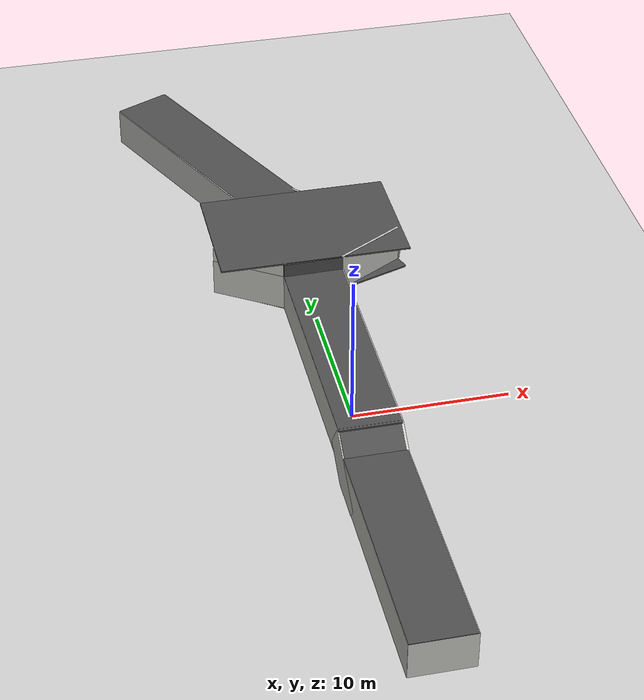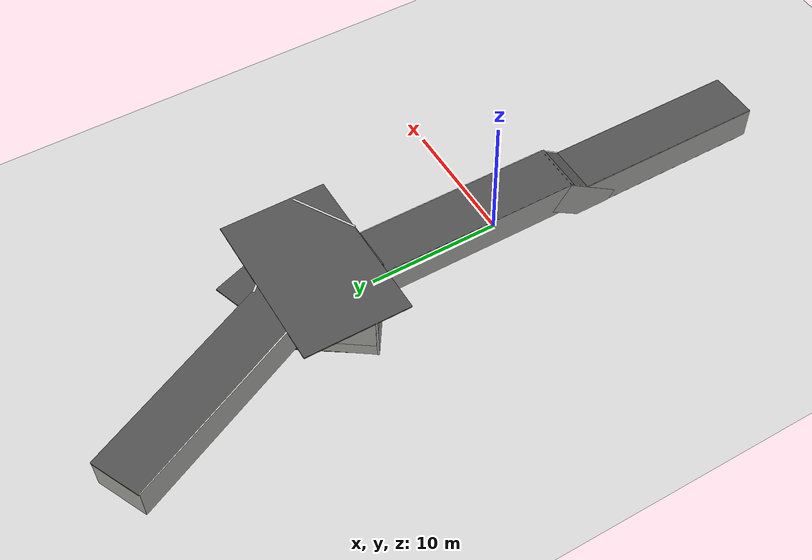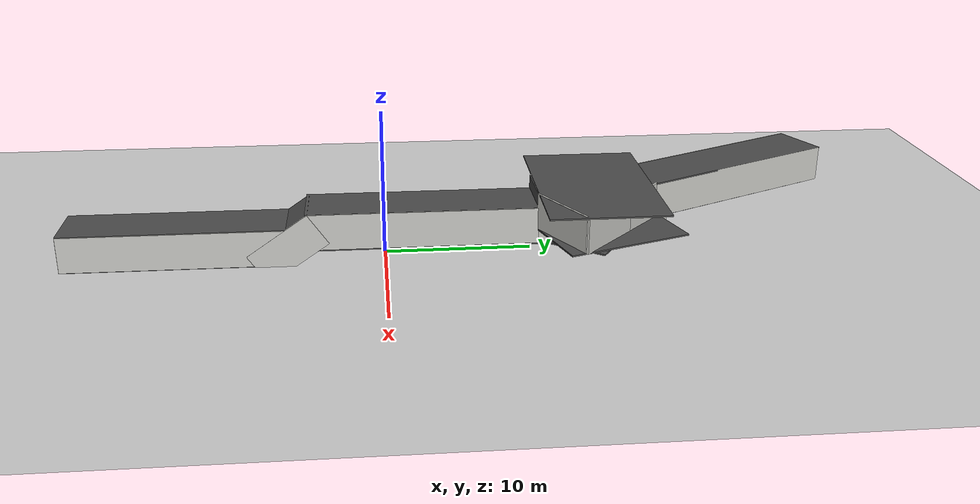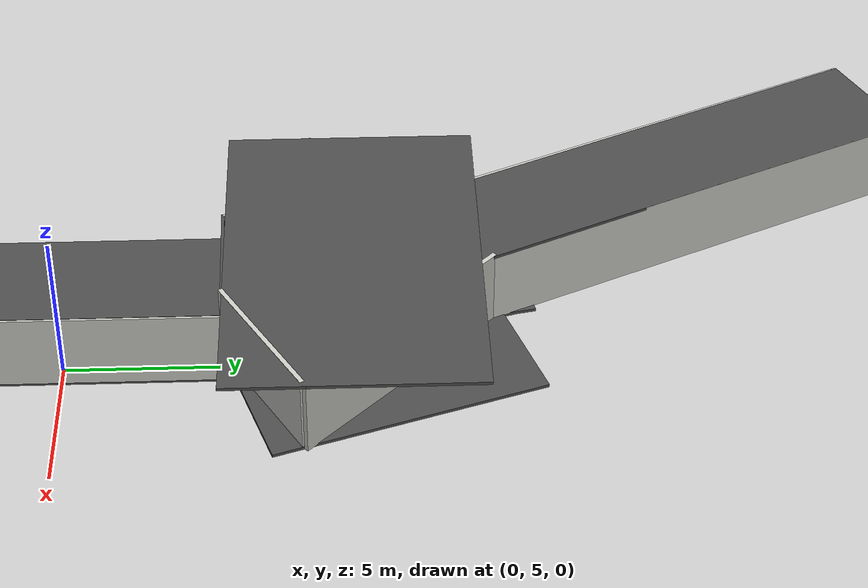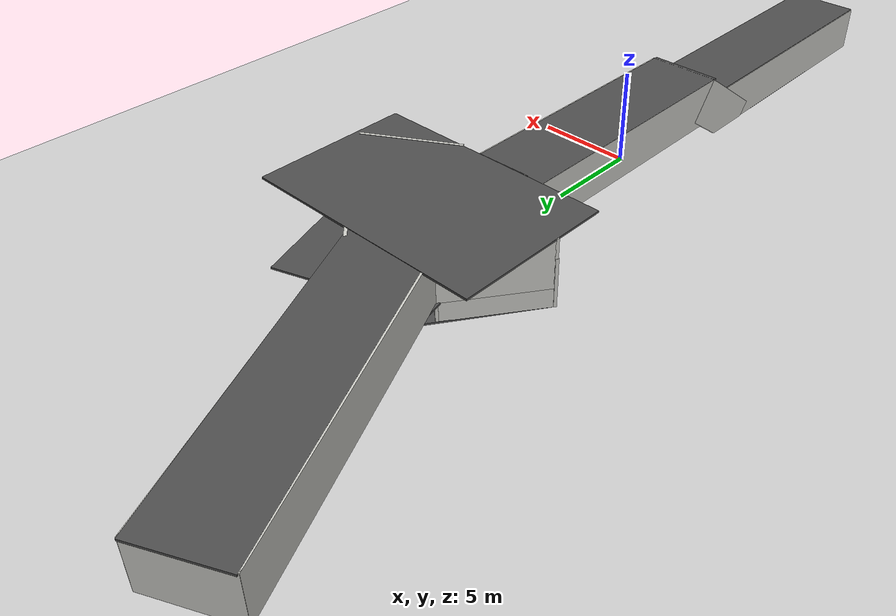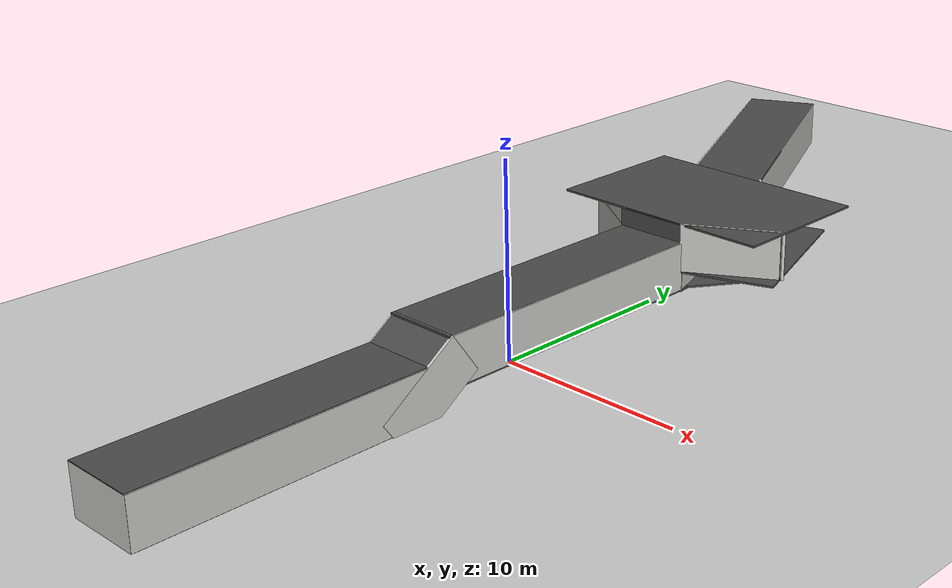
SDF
<sdf version="1.6">
 <world name="default">
  <light name="sun" type="directional">
   <pose>0 0 10 0 -0 0</pose>
   <diffuse>0.8 0.8 0.8 1</diffuse>
   <specular>0.2 0.2 0.2 1</specular>
   <attenuation>
    <range>1000</range>
    <constant>0.9</constant>
    <linear>0.01</linear>
    <quadratic>0.001</quadratic>
   </attenuation>
   <direction>-0.5 0.1 -0.9</direction>
  </light>
  <model name="ground_plane">
   <static>1</static>
   <link name="link">
    <collision name="collision">
     <geometry><plane><normal>0 0 1</normal><size>100 100</size></plane></geometry>
     <surface><friction><ode><mu>100</mu><mu2>50</mu2></ode></friction></surface>
    </collision>
    <visual name="visual">
     <cast_shadows>0</cast_shadows>
     <geometry><plane><normal>0 0 1</normal><size>100 100</size></plane></geometry>
     <material>
      <script><uri>file://media/materials/scripts/gazebo.material</uri><name>Gazebo/Grey</name></script>
     </material>
    </visual>
   </link>
  </model>
  <physics name="default_physics" default="0" type="ode">
   <gravity>0 0 -9.8066</gravity>
   <ode>
    <solver>
     <type>quick</type>
     <iters>10</iters>
     <sor>1.3</sor>
     <use_dynamic_moi_rescaling>0</use_dynamic_moi_rescaling>
    </solver>
    <constraints>
     <cfm>0</cfm>
     <erp>0.2</erp>
     <contact_max_correcting_vel>100</contact_max_correcting_vel>
     <contact_surface_layer>0.001</contact_surface_layer>
    </constraints>
   </ode>
   <max_step_size>0.004</max_step_size>
   <real_time_factor>1</real_time_factor>
   <real_time_update_rate>250</real_time_update_rate>
   <magnetic_field>6.0e-6 2.3e-5 -4.2e-5</magnetic_field>
  </physics>
  <scene><ambient>0.4 0.4 0.4 1</ambient><background>0.7 0.7 0.7 1</background><shadows>1</shadows></scene>
  <spherical_coordinates>
   <surface_model>EARTH_WGS84</surface_model>
   <latitude_deg>0</latitude_deg>
   <longitude_deg>0</longitude_deg>
   <elevation>0</elevation>
   <heading_deg>0</heading_deg>
  </spherical_coordinates>
  <model name="Untitled_1">
   <link name="Wall_6">
    <pose>-0.52874 -7.68161 0 0 -0 0</pose>
    <inertial>
     <inertia><ixx>0</ixx><ixy>0</ixy><ixz>0</ixz><iyy>0</iyy><iyz>0</iyz><izz>0</izz></inertia>
     <mass>0</mass>
    </inertial>
    <visual name="Wall_6_Visual">
     <pose>0 0 1.25 0 -0 0</pose>
     <geometry><box><size>3.91776 0.15 2.5</size></box></geometry>
     <material>
      <script><uri>file://media/materials/scripts/gazebo.material</uri><name>Gazebo/CeilingTiled</name></script>
      <ambient>1 1 1 1</ambient>
      <shader type="pixel"/>
     </material>
     <meta><layer>0</layer></meta>
    </visual>
    <collision name="Wall_6_Collision">
     <pose>0 0 1.25 0 -0 0</pose>
     <geometry><box><size>3.91776 0.15 2.5</size></box></geometry>
     <surface>
      <friction>
       <ode><mu>1</mu><mu2>1</mu2><fdir1>0 0 0</fdir1><slip1>0</slip1><slip2>0</slip2></ode>
       <torsional>
        <coefficient>1</coefficient>
        <patch_radius>0</patch_radius>
        <surface_radius>0</surface_radius>
        <use_patch_radius>1</use_patch_radius>
        <ode><slip>0</slip></ode>
       </torsional>
      </friction>
      <bounce><restitution_coefficient>0</restitution_coefficient><threshold>1e+06</threshold></bounce>
      <contact>
       <collide_without_contact>0</collide_without_contact>
       <collide_without_contact_bitmask>1</collide_without_contact_bitmask>
       <collide_bitmask>1</collide_bitmask>
       <ode>
        <soft_cfm>0</soft_cfm>
        <soft_erp>0.2</soft_erp>
        <kp>1e+13</kp>
        <kd>1</kd>
        <max_vel>0.01</max_vel>
        <min_depth>0</min_depth>
       </ode>
       <bullet>
        <split_impulse>1</split_impulse>
        <split_impulse_penetration_threshold>-0.01</split_impulse_penetration_threshold>
        <soft_cfm>0</soft_cfm>
        <soft_erp>0.2</soft_erp>
        <kp>1e+13</kp>
        <kd>1</kd>
       </bullet>
      </contact>
     </surface>
    </collision>
   </link>
   <link name="Wall_7">
    <pose>1.35961 -5e-06 -0 0 -0 1.5708</pose>
    <visual name="Wall_7_Visual">
     <pose>0 0 1.25 0 -0 0</pose>
     <geometry><box><size>15.5 0.15 2.5</size></box></geometry>
     <material>
      <script><uri>file://media/materials/scripts/gazebo.material</uri><name>Gazebo/CeilingTiled</name></script>
      <ambient>1 1 1 1</ambient>
      <shader type="pixel"/>
     </material>
     <meta><layer>0</layer></meta>
    </visual>
    <collision name="Wall_7_Collision">
     <pose>0 0 1.25 0 -0 0</pose>
     <geometry><box><size>15.5 0.15 2.5</size></box></geometry>
     <surface>
      <friction>
       <ode><mu>1</mu><mu2>1</mu2><fdir1>0 0 0</fdir1><slip1>0</slip1><slip2>0</slip2></ode>
       <torsional>
        <coefficient>1</coefficient>
        <patch_radius>0</patch_radius>
        <surface_radius>0</surface_radius>
        <use_patch_radius>1</use_patch_radius>
        <ode><slip>0</slip></ode>
       </torsional>
      </friction>
      <bounce><restitution_coefficient>0</restitution_coefficient><threshold>1e+06</threshold></bounce>
      <contact>
       <collide_without_contact>0</collide_without_contact>
       <collide_without_contact_bitmask>1</collide_without_contact_bitmask>
       <collide_bitmask>1</collide_bitmask>
       <ode>
        <soft_cfm>0</soft_cfm>
        <soft_erp>0.2</soft_erp>
        <kp>1e+13</kp>
        <kd>1</kd>
        <max_vel>0.01</max_vel>
        <min_depth>0</min_depth>
       </ode>
       <bullet>
        <split_impulse>1</split_impulse>
        <split_impulse_penetration_threshold>-0.01</split_impulse_penetration_threshold>
        <soft_cfm>0</soft_cfm>
        <soft_erp>0.2</soft_erp>
        <kp>1e+13</kp>
        <kd>1</kd>
       </bullet>
      </contact>
     </surface>
    </collision>
   </link>
   <link name="Wall_9">
    <pose>-2.425 0 0 0 -0 1.5708</pose>
    <visual name="Wall_9_Visual">
     <pose>0 0 1.25 0 -0 0</pose>
     <geometry><box><size>15.5 0.15 2.5</size></box></geometry>
     <material>
      <script><uri>file://media/materials/scripts/gazebo.material</uri><name>Gazebo/CeilingTiled</name></script>
      <ambient>1 1 1 1</ambient>
      <shader type="pixel"/>
     </material>
     <meta><layer>0</layer></meta>
    </visual>
    <collision name="Wall_9_Collision">
     <pose>0 0 1.25 0 -0 0</pose>
     <geometry><box><size>15.5 0.15 2.5</size></box></geometry>
     <surface>
      <friction>
       <ode><mu>1</mu><mu2>1</mu2><fdir1>0 0 0</fdir1><slip1>0</slip1><slip2>0</slip2></ode>
       <torsional>
        <coefficient>1</coefficient>
        <patch_radius>0</patch_radius>
        <surface_radius>0</surface_radius>
        <use_patch_radius>1</use_patch_radius>
        <ode><slip>0</slip></ode>
       </torsional>
      </friction>
      <bounce><restitution_coefficient>0</restitution_coefficient><threshold>1e+06</threshold></bounce>
      <contact>
       <collide_without_contact>0</collide_without_contact>
       <collide_without_contact_bitmask>1</collide_without_contact_bitmask>
       <collide_bitmask>1</collide_bitmask>
       <ode>
        <soft_cfm>0</soft_cfm>
        <soft_erp>0.2</soft_erp>
        <kp>1e+13</kp>
        <kd>1</kd>
        <max_vel>0.01</max_vel>
        <min_depth>0</min_depth>
       </ode>
       <bullet>
        <split_impulse>1</split_impulse>
        <split_impulse_penetration_threshold>-0.01</split_impulse_penetration_threshold>
        <soft_cfm>0</soft_cfm>
        <soft_erp>0.2</soft_erp>
        <kp>1e+13</kp>
        <kd>1</kd>
       </bullet>
      </contact>
     </surface>
    </collision>
   </link>
   <static>1</static>
   <pose>0.386993 -13.7674 0 0 -0 0</pose>
  </model>
  <model name="unit_box_0_static_clone">
   <link name="link">
    <inertial>
     <mass>1</mass>
     <inertia>
      <ixx>0.166667</ixx>
      <ixy>0</ixy>
      <ixz>0</ixz>
      <iyy>0.166667</iyy>
      <iyz>0</iyz>
      <izz>0.166667</izz>
     </inertia>
    </inertial>
    <visual name="visual">
     <geometry><box><size>0.092218 3.57895 0.407783</size></box></geometry>
     <material>
      <script><name>Gazebo/Grey</name><uri>file://media/materials/scripts/gazebo.material</uri></script>
      <shader type="pixel"/>
     </material>
    </visual>
    <collision name="collision">
     <geometry><box><size>0.092218 3.57895 0.407783</size></box></geometry>
     <surface>
      <friction>
       <ode><mu>1</mu><mu2>1</mu2><fdir1>0 0 0</fdir1><slip1>0</slip1><slip2>0</slip2></ode>
       <torsional>
        <coefficient>1</coefficient>
        <patch_radius>0</patch_radius>
        <surface_radius>0</surface_radius>
        <use_patch_radius>1</use_patch_radius>
        <ode><slip>0</slip></ode>
       </torsional>
      </friction>
      <bounce><restitution_coefficient>0</restitution_coefficient><threshold>1e+06</threshold></bounce>
      <contact>
       <collide_without_contact>0</collide_without_contact>
       <collide_without_contact_bitmask>1</collide_without_contact_bitmask>
       <collide_bitmask>1</collide_bitmask>
       <ode>
        <soft_cfm>0</soft_cfm>
        <soft_erp>0.2</soft_erp>
        <kp>1e+13</kp>
        <kd>1</kd>
        <max_vel>0.01</max_vel>
        <min_depth>0</min_depth>
       </ode>
       <bullet>
        <split_impulse>1</split_impulse>
        <split_impulse_penetration_threshold>-0.01</split_impulse_penetration_threshold>
        <soft_cfm>0</soft_cfm>
        <soft_erp>0.2</soft_erp>
        <kp>1e+13</kp>
        <kd>1</kd>
       </bullet>
      </contact>
     </surface>
    </collision>
   </link>
   <static>1</static>
   <pose>-0.122546 -5.98751 0.220308 0 0 -1.5707</pose>
  </model>
  <light name="user_point_light_0" type="point">
   <pose>-0.303887 -6.76927 1 0 -0 0</pose>
   <diffuse>0.5 0.5 0.5 1</diffuse>
   <specular>0.1 0.1 0.1 1</specular>
   <attenuation>
    <range>20</range>
    <constant>0.5</constant>
    <linear>0.01</linear>
    <quadratic>0.001</quadratic>
   </attenuation>
   <cast_shadows>0</cast_shadows>
   <direction>0 0 -1</direction>
  </light>
  <model name="unit_box_0_static_clone_0">
   <link name="link">
    <inertial>
     <mass>1</mass>
     <inertia>
      <ixx>0.166667</ixx>
      <ixy>0</ixy>
      <ixz>0</ixz>
      <iyy>0.166667</iyy>
      <iyz>0</iyz>
      <izz>0.166667</izz>
     </inertia>
    </inertial>
    <visual name="visual">
     <geometry><box><size>0.092218 3.57895 0.407783</size></box></geometry>
     <material>
      <script><name>Gazebo/Grey</name><uri>file://media/materials/scripts/gazebo.material</uri></script>
      <shader type="pixel"/>
     </material>
    </visual>
    <collision name="collision">
     <geometry><box><size>0.092218 3.57895 0.407783</size></box></geometry>
     <surface>
      <friction>
       <ode><mu>1</mu><mu2>1</mu2><fdir1>0 0 0</fdir1><slip1>0</slip1><slip2>0</slip2></ode>
       <torsional>
        <coefficient>1</coefficient>
        <patch_radius>0</patch_radius>
        <surface_radius>0</surface_radius>
        <use_patch_radius>1</use_patch_radius>
        <ode><slip>0</slip></ode>
       </torsional>
      </friction>
      <bounce><restitution_coefficient>0</restitution_coefficient><threshold>1e+06</threshold></bounce>
      <contact>
       <collide_without_contact>0</collide_without_contact>
       <collide_without_contact_bitmask>1</collide_without_contact_bitmask>
       <collide_bitmask>1</collide_bitmask>
       <ode>
        <soft_cfm>0</soft_cfm>
        <soft_erp>0.2</soft_erp>
        <kp>1e+13</kp>
        <kd>1</kd>
        <max_vel>0.01</max_vel>
        <min_depth>0</min_depth>
       </ode>
       <bullet>
        <split_impulse>1</split_impulse>
        <split_impulse_penetration_threshold>-0.01</split_impulse_penetration_threshold>
        <soft_cfm>0</soft_cfm>
        <soft_erp>0.2</soft_erp>
        <kp>1e+13</kp>
        <kd>1</kd>
       </bullet>
      </contact>
     </surface>
    </collision>
   </link>
   <static>1</static>
   <pose>-0.130791 -5.76028 0.422576 0 0 -1.5707</pose>
  </model>
  <model name="unit_box_0_static_clone_0_clone">
   <link name="link">
    <inertial>
     <mass>1</mass>
     <inertia>
      <ixx>0.166667</ixx>
      <ixy>0</ixy>
      <ixz>0</ixz>
      <iyy>0.166667</iyy>
      <iyz>0</iyz>
      <izz>0.166667</izz>
     </inertia>
    </inertial>
    <visual name="visual">
     <geometry><box><size>0.092218 3.57895 0.407783</size></box></geometry>
     <material>
      <script><name>Gazebo/Grey</name><uri>file://media/materials/scripts/gazebo.material</uri></script>
      <shader type="pixel"/>
     </material>
    </visual>
    <collision name="collision">
     <geometry><box><size>0.092218 3.57895 0.407783</size></box></geometry>
     <surface>
      <friction>
       <ode><mu>1</mu><mu2>1</mu2><fdir1>0 0 0</fdir1><slip1>0</slip1><slip2>0</slip2></ode>
       <torsional>
        <coefficient>1</coefficient>
        <patch_radius>0</patch_radius>
        <surface_radius>0</surface_radius>
        <use_patch_radius>1</use_patch_radius>
        <ode><slip>0</slip></ode>
       </torsional>
      </friction>
      <bounce><restitution_coefficient>0</restitution_coefficient><threshold>1e+06</threshold></bounce>
      <contact>
       <collide_without_contact>0</collide_without_contact>
       <collide_without_contact_bitmask>1</collide_without_contact_bitmask>
       <collide_bitmask>1</collide_bitmask>
       <ode>
        <soft_cfm>0</soft_cfm>
        <soft_erp>0.2</soft_erp>
        <kp>1e+13</kp>
        <kd>1</kd>
        <max_vel>0.01</max_vel>
        <min_depth>0</min_depth>
       </ode>
       <bullet>
        <split_impulse>1</split_impulse>
        <split_impulse_penetration_threshold>-0.01</split_impulse_penetration_threshold>
        <soft_cfm>0</soft_cfm>
        <soft_erp>0.2</soft_erp>
        <kp>1e+13</kp>
        <kd>1</kd>
       </bullet>
      </contact>
     </surface>
    </collision>
   </link>
   <static>1</static>
   <pose>-0.123897 -5.5252 0.62338 0 0 -1.5707</pose>
  </model>
  <model name="unit_box_0_static_clone_0_clone_clone">
   <link name="link">
    <inertial>
     <mass>1</mass>
     <inertia>
      <ixx>0.166667</ixx>
      <ixy>0</ixy>
      <ixz>0</ixz>
      <iyy>0.166667</iyy>
      <iyz>0</iyz>
      <izz>0.166667</izz>
     </inertia>
    </inertial>
    <visual name="visual">
     <geometry><box><size>0.092218 3.57895 0.407783</size></box></geometry>
     <material>
      <script><name>Gazebo/Grey</name><uri>file://media/materials/scripts/gazebo.material</uri></script>
      <shader type="pixel"/>
     </material>
    </visual>
    <collision name="collision">
     <geometry><box><size>0.092218 3.57895 0.407783</size></box></geometry>
     <surface>
      <friction>
       <ode><mu>1</mu><mu2>1</mu2><fdir1>0 0 0</fdir1><slip1>0</slip1><slip2>0</slip2></ode>
       <torsional>
        <coefficient>1</coefficient>
        <patch_radius>0</patch_radius>
        <surface_radius>0</surface_radius>
        <use_patch_radius>1</use_patch_radius>
        <ode><slip>0</slip></ode>
       </torsional>
      </friction>
      <bounce><restitution_coefficient>0</restitution_coefficient><threshold>1e+06</threshold></bounce>
      <contact>
       <collide_without_contact>0</collide_without_contact>
       <collide_without_contact_bitmask>1</collide_without_contact_bitmask>
       <collide_bitmask>1</collide_bitmask>
       <ode>
        <soft_cfm>0</soft_cfm>
        <soft_erp>0.2</soft_erp>
        <kp>1e+13</kp>
        <kd>1</kd>
        <max_vel>0.01</max_vel>
        <min_depth>0</min_depth>
       </ode>
       <bullet>
        <split_impulse>1</split_impulse>
        <split_impulse_penetration_threshold>-0.01</split_impulse_penetration_threshold>
        <soft_cfm>0</soft_cfm>
        <soft_erp>0.2</soft_erp>
        <kp>1e+13</kp>
        <kd>1</kd>
       </bullet>
      </contact>
     </surface>
    </collision>
   </link>
   <static>1</static>
   <pose>-0.128111 -5.29185 0.822943 0 0 -1.5707</pose>
  </model>
  <model name="Untitled_1_0_clone_0">
   <pose>-3.71194 -5.73886 0.077716 0 -0.606196 1.5707</pose>
   <link name="Wall_16">
    <collision name="Wall_16_Collision">
     <geometry><box><size>5 0.15 2.5</size></box></geometry>
     <pose>0 0 1.25 0 -0 0</pose>
    </collision>
    <visual name="Wall_16_Visual">
     <pose>0 0 1.25 0 -0 0</pose>
     <geometry><box><size>5 0.15 2.5</size></box></geometry>
     <material>
      <script><uri>file://media/materials/scripts/gazebo.material</uri><name>Gazebo/CeilingTiled</name></script>
      <ambient>1 1 1 1</ambient>
     </material>
     <meta><layer>0</layer></meta>
    </visual>
    <pose>0 -1.66958 0 0 -0 0</pose>
   </link>
   <static>1</static>
  </model>
  <model name="Untitled_1_clone">
   <link name="Wall_7">
    <pose>1.35961 -5e-06 0 0 -0 1.5708</pose>
    <visual name="Wall_7_Visual">
     <pose>0 0 1.25 0 -0 0</pose>
     <geometry><box><size>15.5 0.15 2.5</size></box></geometry>
     <material>
      <script><uri>file://media/materials/scripts/gazebo.material</uri><name>Gazebo/CeilingTiled</name></script>
      <ambient>1 1 1 1</ambient>
      <shader type="pixel"/>
     </material>
     <meta><layer>0</layer></meta>
    </visual>
    <collision name="Wall_7_Collision">
     <pose>0 0 1.25 0 -0 0</pose>
     <geometry><box><size>15.5 0.15 2.5</size></box></geometry>
     <surface>
      <friction>
       <ode><mu>1</mu><mu2>1</mu2><fdir1>0 0 0</fdir1><slip1>0</slip1><slip2>0</slip2></ode>
       <torsional>
        <coefficient>1</coefficient>
        <patch_radius>0</patch_radius>
        <surface_radius>0</surface_radius>
        <use_patch_radius>1</use_patch_radius>
        <ode><slip>0</slip></ode>
       </torsional>
      </friction>
      <bounce><restitution_coefficient>0</restitution_coefficient><threshold>1e+06</threshold></bounce>
      <contact>
       <collide_without_contact>0</collide_without_contact>
       <collide_without_contact_bitmask>1</collide_without_contact_bitmask>
       <collide_bitmask>1</collide_bitmask>
       <ode>
        <soft_cfm>0</soft_cfm>
        <soft_erp>0.2</soft_erp>
        <kp>1e+13</kp>
        <kd>1</kd>
        <max_vel>0.01</max_vel>
        <min_depth>0</min_depth>
       </ode>
       <bullet>
        <split_impulse>1</split_impulse>
        <split_impulse_penetration_threshold>-0.01</split_impulse_penetration_threshold>
        <soft_cfm>0</soft_cfm>
        <soft_erp>0.2</soft_erp>
        <kp>1e+13</kp>
        <kd>1</kd>
       </bullet>
      </contact>
     </surface>
    </collision>
   </link>
   <link name="Wall_9">
    <pose>-2.425 0 0 0 -0 1.5708</pose>
    <visual name="Wall_9_Visual">
     <pose>0 0 1.25 0 -0 0</pose>
     <geometry><box><size>15.5 0.15 2.5</size></box></geometry>
     <material>
      <script><uri>file://media/materials/scripts/gazebo.material</uri><name>Gazebo/CeilingTiled</name></script>
      <ambient>1 1 1 1</ambient>
      <shader type="pixel"/>
     </material>
     <meta><layer>0</layer></meta>
    </visual>
    <collision name="Wall_9_Collision">
     <pose>0 0 1.25 0 -0 0</pose>
     <geometry><box><size>15.5 0.15 2.5</size></box></geometry>
     <surface>
      <friction>
       <ode><mu>1</mu><mu2>1</mu2><fdir1>0 0 0</fdir1><slip1>0</slip1><slip2>0</slip2></ode>
       <torsional>
        <coefficient>1</coefficient>
        <patch_radius>0</patch_radius>
        <surface_radius>0</surface_radius>
        <use_patch_radius>1</use_patch_radius>
        <ode><slip>0</slip></ode>
       </torsional>
      </friction>
      <bounce><restitution_coefficient>0</restitution_coefficient><threshold>1e+06</threshold></bounce>
      <contact>
       <collide_without_contact>0</collide_without_contact>
       <collide_without_contact_bitmask>1</collide_without_contact_bitmask>
       <collide_bitmask>1</collide_bitmask>
       <ode>
        <soft_cfm>0</soft_cfm>
        <soft_erp>0.2</soft_erp>
        <kp>1e+13</kp>
        <kd>1</kd>
        <max_vel>0.01</max_vel>
        <min_depth>0</min_depth>
       </ode>
       <bullet>
        <split_impulse>1</split_impulse>
        <split_impulse_penetration_threshold>-0.01</split_impulse_penetration_threshold>
        <soft_cfm>0</soft_cfm>
        <soft_erp>0.2</soft_erp>
        <kp>1e+13</kp>
        <kd>1</kd>
       </bullet>
      </contact>
     </surface>
    </collision>
   </link>
   <static>1</static>
   <pose>0.39999 2.62887 1.05101 0 -0 0</pose>
  </model>
  <model name="Untitled_1_0_clone_0_clone">
   <pose>0.09083 -5.76541 0.077716 0 -0.606196 1.5707</pose>
   <link name="Wall_16">
    <collision name="Wall_16_Collision">
     <geometry><box><size>5 0.15 2.5</size></box></geometry>
     <pose>0 0 1.25 0 -0 0</pose>
    </collision>
    <visual name="Wall_16_Visual">
     <pose>0 0 1.25 0 -0 0</pose>
     <geometry><box><size>5 0.15 2.5</size></box></geometry>
     <material>
      <script><uri>file://media/materials/scripts/gazebo.material</uri><name>Gazebo/CeilingTiled</name></script>
      <ambient>1 1 1 1</ambient>
     </material>
     <meta><layer>0</layer></meta>
    </visual>
    <pose>0 -1.66958 0 0 -0 0</pose>
   </link>
   <static>1</static>
  </model>
  <model name="Untitled_1_0_clone">
   <pose>-4.9863 10.2711 1.05157 0 -0 2.56674</pose>
   <link name="Wall_16">
    <collision name="Wall_16_Collision">
     <geometry><box><size>5 0.15 2.5</size></box></geometry>
     <pose>0 0 1.25 0 -0 0</pose>
    </collision>
    <visual name="Wall_16_Visual">
     <pose>0 0 1.25 0 -0 0</pose>
     <geometry><box><size>5 0.15 2.5</size></box></geometry>
     <material>
      <script><uri>file://media/materials/scripts/gazebo.material</uri><name>Gazebo/CeilingTiled</name></script>
      <ambient>1 1 1 1</ambient>
     </material>
     <meta><layer>0</layer></meta>
    </visual>
    <pose>0 -1.66958 0 0 -0 0</pose>
   </link>
   <static>1</static>
  </model>
  <model name="Untitled_1_0_clone_clone">
   <pose>-5.9653 16.0414 1.05157 0 -0 0.949354</pose>
   <link name="Wall_16">
    <collision name="Wall_16_Collision">
     <geometry><box><size>5 0.15 2.5</size></box></geometry>
     <pose>0 0 1.25 0 -0 0</pose>
    </collision>
    <visual name="Wall_16_Visual">
     <pose>0 0 1.25 0 -0 0</pose>
     <geometry><box><size>5 0.15 2.5</size></box></geometry>
     <material>
      <script><uri>file://media/materials/scripts/gazebo.material</uri><name>Gazebo/CeilingTiled</name></script>
      <ambient>1 1 1 1</ambient>
     </material>
     <meta><layer>0</layer></meta>
    </visual>
    <pose>0 -1.66958 0 0 -0 0</pose>
   </link>
   <static>1</static>
  </model>
  <model name="Untitled_1_clone_0">
   <link name="Wall_6">
    <pose>-0.52874 -7.68161 0 0 -0 0</pose>
    <inertial>
     <inertia><ixx>0</ixx><ixy>0</ixy><ixz>0</ixz><iyy>0</iyy><iyz>0</iyz><izz>0</izz></inertia>
     <mass>0</mass>
    </inertial>
    <visual name="Wall_6_Visual">
     <pose>0 0 1.25 0 -0 0</pose>
     <geometry><box><size>3.91776 0.15 2.5</size></box></geometry>
     <material>
      <script><uri>file://media/materials/scripts/gazebo.material</uri><name>Gazebo/CeilingTiled</name></script>
      <ambient>1 1 1 1</ambient>
      <shader type="pixel"/>
     </material>
     <meta><layer>0</layer></meta>
    </visual>
    <collision name="Wall_6_Collision">
     <pose>0 0 1.25 0 -0 0</pose>
     <geometry><box><size>3.91776 0.15 2.5</size></box></geometry>
     <surface>
      <friction>
       <ode><mu>1</mu><mu2>1</mu2><fdir1>0 0 0</fdir1><slip1>0</slip1><slip2>0</slip2></ode>
       <torsional>
        <coefficient>1</coefficient>
        <patch_radius>0</patch_radius>
        <surface_radius>0</surface_radius>
        <use_patch_radius>1</use_patch_radius>
        <ode><slip>0</slip></ode>
       </torsional>
      </friction>
      <bounce><restitution_coefficient>0</restitution_coefficient><threshold>1e+06</threshold></bounce>
      <contact>
       <collide_without_contact>0</collide_without_contact>
       <collide_without_contact_bitmask>1</collide_without_contact_bitmask>
       <collide_bitmask>1</collide_bitmask>
       <ode>
        <soft_cfm>0</soft_cfm>
        <soft_erp>0.2</soft_erp>
        <kp>1e+13</kp>
        <kd>1</kd>
        <max_vel>0.01</max_vel>
        <min_depth>0</min_depth>
       </ode>
       <bullet>
        <split_impulse>1</split_impulse>
        <split_impulse_penetration_threshold>-0.01</split_impulse_penetration_threshold>
        <soft_cfm>0</soft_cfm>
        <soft_erp>0.2</soft_erp>
        <kp>1e+13</kp>
        <kd>1</kd>
       </bullet>
      </contact>
     </surface>
    </collision>
   </link>
   <link name="Wall_7">
    <pose>1.35961 -5e-06 -0 0 -0 1.5708</pose>
    <visual name="Wall_7_Visual">
     <pose>0 0 1.25 0 -0 0</pose>
     <geometry><box><size>15.5 0.15 2.5</size></box></geometry>
     <material>
      <script><uri>file://media/materials/scripts/gazebo.material</uri><name>Gazebo/CeilingTiled</name></script>
      <ambient>1 1 1 1</ambient>
      <shader type="pixel"/>
     </material>
     <meta><layer>0</layer></meta>
    </visual>
    <collision name="Wall_7_Collision">
     <pose>0 0 1.25 0 -0 0</pose>
     <geometry><box><size>15.5 0.15 2.5</size></box></geometry>
     <surface>
      <friction>
       <ode><mu>1</mu><mu2>1</mu2><fdir1>0 0 0</fdir1><slip1>0</slip1><slip2>0</slip2></ode>
       <torsional>
        <coefficient>1</coefficient>
        <patch_radius>0</patch_radius>
        <surface_radius>0</surface_radius>
        <use_patch_radius>1</use_patch_radius>
        <ode><slip>0</slip></ode>
       </torsional>
      </friction>
      <bounce><restitution_coefficient>0</restitution_coefficient><threshold>1e+06</threshold></bounce>
      <contact>
       <collide_without_contact>0</collide_without_contact>
       <collide_without_contact_bitmask>1</collide_without_contact_bitmask>
       <collide_bitmask>1</collide_bitmask>
       <ode>
        <soft_cfm>0</soft_cfm>
        <soft_erp>0.2</soft_erp>
        <kp>1e+13</kp>
        <kd>1</kd>
        <max_vel>0.01</max_vel>
        <min_depth>0</min_depth>
       </ode>
       <bullet>
        <split_impulse>1</split_impulse>
        <split_impulse_penetration_threshold>-0.01</split_impulse_penetration_threshold>
        <soft_cfm>0</soft_cfm>
        <soft_erp>0.2</soft_erp>
        <kp>1e+13</kp>
        <kd>1</kd>
       </bullet>
      </contact>
     </surface>
    </collision>
   </link>
   <link name="Wall_9">
    <pose>-2.425 0 0 0 -0 1.5708</pose>
    <visual name="Wall_9_Visual">
     <pose>0 0 1.25 0 -0 0</pose>
     <geometry><box><size>15.5 0.15 2.5</size></box></geometry>
     <material>
      <script><uri>file://media/materials/scripts/gazebo.material</uri><name>Gazebo/CeilingTiled</name></script>
      <ambient>1 1 1 1</ambient>
      <shader type="pixel"/>
     </material>
     <meta><layer>0</layer></meta>
    </visual>
    <collision name="Wall_9_Collision">
     <pose>0 0 1.25 0 -0 0</pose>
     <geometry><box><size>15.5 0.15 2.5</size></box></geometry>
     <surface>
      <friction>
       <ode><mu>1</mu><mu2>1</mu2><fdir1>0 0 0</fdir1><slip1>0</slip1><slip2>0</slip2></ode>
       <torsional>
        <coefficient>1</coefficient>
        <patch_radius>0</patch_radius>
        <surface_radius>0</surface_radius>
        <use_patch_radius>1</use_patch_radius>
        <ode><slip>0</slip></ode>
       </torsional>
      </friction>
      <bounce><restitution_coefficient>0</restitution_coefficient><threshold>1e+06</threshold></bounce>
      <contact>
       <collide_without_contact>0</collide_without_contact>
       <collide_without_contact_bitmask>1</collide_without_contact_bitmask>
       <collide_bitmask>1</collide_bitmask>
       <ode>
        <soft_cfm>0</soft_cfm>
        <soft_erp>0.2</soft_erp>
        <kp>1e+13</kp>
        <kd>1</kd>
        <max_vel>0.01</max_vel>
        <min_depth>0</min_depth>
       </ode>
       <bullet>
        <split_impulse>1</split_impulse>
        <split_impulse_penetration_threshold>-0.01</split_impulse_penetration_threshold>
        <soft_cfm>0</soft_cfm>
        <soft_erp>0.2</soft_erp>
        <kp>1e+13</kp>
        <kd>1</kd>
       </bullet>
      </contact>
     </surface>
    </collision>
   </link>
   <static>1</static>
   <pose>-5.16972 24.5982 2.02784 0 0 -2.7042</pose>
  </model>
  <model name="Untitled_1_0_clone_clone_0">
   <pose>0.845159 15.7579 2.03023 0 -0 2.36363</pose>
   <link name="Wall_16">
    <collision name="Wall_16_Collision">
     <geometry><box><size>5 0.15 2.5</size></box></geometry>
     <pose>0 0 1.25 0 -0 0</pose>
    </collision>
    <visual name="Wall_16_Visual">
     <pose>0 0 1.25 0 -0 0</pose>
     <geometry><box><size>5 0.15 2.5</size></box></geometry>
     <material>
      <script><uri>file://media/materials/scripts/gazebo.material</uri><name>Gazebo/CeilingTiled</name></script>
      <ambient>1 1 1 1</ambient>
     </material>
     <meta><layer>0</layer></meta>
    </visual>
    <pose>0 -1.66958 0 0 -0 0</pose>
   </link>
   <static>1</static>
  </model>
  <model name="Untitled_1_0_clone_clone_clone">
   <pose>3.06138 12.9911 2.05939 0 -0 0.522456</pose>
   <link name="Wall_16">
    <collision name="Wall_16_Collision">
     <geometry><box><size>5 0.15 2.5</size></box></geometry>
     <pose>0 0 1.25 0 -0 0</pose>
    </collision>
    <visual name="Wall_16_Visual">
     <pose>0 0 1.25 0 -0 0</pose>
     <geometry><box><size>5 0.15 2.5</size></box></geometry>
     <material>
      <script><uri>file://media/materials/scripts/gazebo.material</uri><name>Gazebo/CeilingTiled</name></script>
      <ambient>1 1 1 1</ambient>
     </material>
     <meta><layer>0</layer></meta>
    </visual>
    <pose>0 -1.66958 0 0 -0 0</pose>
   </link>
   <static>1</static>
  </model>
  <model name="Untitled_1_0">
   <link name="Wall_16">
    <pose>3.00166 1.24778 0.309228 0 -0 0.121595</pose>
    <inertial>
     <inertia><ixx>0</ixx><ixy>0</ixy><ixz>0</ixz><iyy>0</iyy><iyz>0</iyz><izz>0</izz></inertia>
     <mass>0</mass>
    </inertial>
    <visual name="Wall_16_Visual">
     <pose>0 0 1.25 0 -0 0</pose>
     <geometry><box><size>10.144 0.15 1.04032</size></box></geometry>
     <material>
      <script><uri>file://media/materials/scripts/gazebo.material</uri><name>Gazebo/CeilingTiled</name></script>
      <ambient>1 1 1 1</ambient>
      <shader type="pixel"/>
     </material>
     <meta><layer>0</layer></meta>
    </visual>
    <collision name="Wall_16_Collision">
     <pose>0 0 1.25 0 -0 0</pose>
     <geometry><box><size>10.144 0.15 1.04032</size></box></geometry>
     <surface>
      <friction>
       <ode><mu>1</mu><mu2>1</mu2><fdir1>0 0 0</fdir1><slip1>0</slip1><slip2>0</slip2></ode>
       <torsional>
        <coefficient>1</coefficient>
        <patch_radius>0</patch_radius>
        <surface_radius>0</surface_radius>
        <use_patch_radius>1</use_patch_radius>
        <ode><slip>0</slip></ode>
       </torsional>
      </friction>
      <bounce><restitution_coefficient>0</restitution_coefficient><threshold>1e+06</threshold></bounce>
      <contact>
       <collide_without_contact>0</collide_without_contact>
       <collide_without_contact_bitmask>1</collide_without_contact_bitmask>
       <collide_bitmask>1</collide_bitmask>
       <ode>
        <soft_cfm>0</soft_cfm>
        <soft_erp>0.2</soft_erp>
        <kp>1e+13</kp>
        <kd>1</kd>
        <max_vel>0.01</max_vel>
        <min_depth>0</min_depth>
       </ode>
       <bullet>
        <split_impulse>1</split_impulse>
        <split_impulse_penetration_threshold>-0.01</split_impulse_penetration_threshold>
        <soft_cfm>0</soft_cfm>
        <soft_erp>0.2</soft_erp>
        <kp>1e+13</kp>
        <kd>1</kd>
       </bullet>
      </contact>
     </surface>
    </collision>
   </link>
   <static>1</static>
   <pose>2.00853 12.4355 -0.110255 0 -0 1.7692</pose>
  </model>
  <model name="asphalt_plane_clone_clone_clone_clone">
   <static>1</static>
   <link name="link">
    <collision name="collision"><geometry><box><size>3.67524 15.0034 0.1</size></box></geometry></collision>
    <visual name="visual">
     <cast_shadows>0</cast_shadows>
     <geometry><box><size>3.67524 15.0034 0.1</size></box></geometry>
     <material>
      <script>
       <uri>model://asphalt_plane/materials/scripts</uri>
       <uri>model://asphalt_plane/materials/textures</uri>
       <name>vrc/asphalt</name>
      </script>
     </material>
    </visual>
   </link>
   <pose>-4.67974 24.8418 2.01114 0 -0 0.438323</pose>
  </model>
  <model name="Untitled_1_0_clone_clone_0_clone">
   <pose>3.25433 13.4028 2.03023 0 -0 2.36363</pose>
   <link name="Wall_16">
    <collision name="Wall_16_Collision">
     <geometry><box><size>5 0.15 2.5</size></box></geometry>
     <pose>0 0 1.25 0 -0 0</pose>
    </collision>
    <visual name="Wall_16_Visual">
     <pose>0 0 1.25 0 -0 0</pose>
     <geometry><box><size>5 0.15 2.5</size></box></geometry>
     <material>
      <script><uri>file://media/materials/scripts/gazebo.material</uri><name>Gazebo/CeilingTiled</name></script>
      <ambient>1 1 1 1</ambient>
     </material>
     <meta><layer>0</layer></meta>
    </visual>
    <pose>0 -1.66958 0 0 -0 0</pose>
   </link>
   <static>1</static>
  </model>
  <model name="Untitled_1_0_clone_clone_clone_0">
   <pose>-6.04514 15.9304 1.05157 0 -0 0.949354</pose>
   <link name="Wall_16">
    <collision name="Wall_16_Collision">
     <geometry><box><size>5 0.15 2.5</size></box></geometry>
     <pose>0 0 1.25 0 -0 0</pose>
    </collision>
    <visual name="Wall_16_Visual">
     <pose>0 0 1.25 0 -0 0</pose>
     <geometry><box><size>5 0.15 2.5</size></box></geometry>
     <material>
      <script><uri>file://media/materials/scripts/gazebo.material</uri><name>Gazebo/CeilingTiled</name></script>
      <ambient>1 1 1 1</ambient>
     </material>
     <meta><layer>0</layer></meta>
    </visual>
    <pose>0 -1.66958 0 0 -0 0</pose>
   </link>
   <static>1</static>
  </model>
  <model name="Untitled_1_0_clone_clone_clone_1">
   <pose>-5.96213 16.0475 2.02791 0 -0 0.949354</pose>
   <link name="Wall_16">
    <collision name="Wall_16_Collision">
     <geometry><box><size>5 0.15 2.5</size></box></geometry>
     <pose>0 0 1.25 0 -0 0</pose>
    </collision>
    <visual name="Wall_16_Visual">
     <pose>0 0 1.25 0 -0 0</pose>
     <geometry><box><size>5 0.15 2.5</size></box></geometry>
     <material>
      <script><uri>file://media/materials/scripts/gazebo.material</uri><name>Gazebo/CeilingTiled</name></script>
      <ambient>1 1 1 1</ambient>
     </material>
     <meta><layer>0</layer></meta>
    </visual>
    <pose>0 -1.66958 0 0 -0 0</pose>
   </link>
   <static>1</static>
  </model>
  <model name="Untitled_1_0_clone_clone_1">
   <pose>-4.96028 10.2797 2.03296 0 -0 2.56674</pose>
   <link name="Wall_16">
    <collision name="Wall_16_Collision">
     <geometry><box><size>5 0.15 2.5</size></box></geometry>
     <pose>0 0 1.25 0 -0 0</pose>
    </collision>
    <visual name="Wall_16_Visual">
     <pose>0 0 1.25 0 -0 0</pose>
     <geometry><box><size>5 0.15 2.5</size></box></geometry>
     <material>
      <script><uri>file://media/materials/scripts/gazebo.material</uri><name>Gazebo/CeilingTiled</name></script>
      <ambient>1 1 1 1</ambient>
     </material>
     <meta><layer>0</layer></meta>
    </visual>
    <pose>0 -1.66958 0 0 -0 0</pose>
   </link>
   <static>1</static>
  </model>
  <model name="unit_box_0_static_clone_0_clone_clone_0_clone">
   <link name="link">
    <inertial>
     <mass>1</mass>
     <inertia>
      <ixx>0.166667</ixx>
      <ixy>0</ixy>
      <ixz>0</ixz>
      <iyy>0.166667</iyy>
      <iyz>0</iyz>
      <izz>0.166667</izz>
     </inertia>
    </inertial>
    <visual name="visual">
     <geometry><box><size>0.092218 2.12592 0.294956</size></box></geometry>
     <material>
      <script><name>Gazebo/Grey</name><uri>file://media/materials/scripts/gazebo.material</uri></script>
      <shader type="pixel"/>
     </material>
    </visual>
    <collision name="collision">
     <geometry><box><size>0.092218 2.12592 0.294956</size></box></geometry>
     <surface>
      <friction>
       <ode><mu>1</mu><mu2>1</mu2><fdir1>0 0 0</fdir1><slip1>0</slip1><slip2>0</slip2></ode>
       <torsional>
        <coefficient>1</coefficient>
        <patch_radius>0</patch_radius>
        <surface_radius>0</surface_radius>
        <use_patch_radius>1</use_patch_radius>
        <ode><slip>0</slip></ode>
       </torsional>
      </friction>
      <bounce><restitution_coefficient>0</restitution_coefficient><threshold>1e+06</threshold></bounce>
      <contact>
       <collide_without_contact>0</collide_without_contact>
       <collide_without_contact_bitmask>1</collide_without_contact_bitmask>
       <collide_bitmask>1</collide_bitmask>
       <ode>
        <soft_cfm>0</soft_cfm>
        <soft_erp>0.2</soft_erp>
        <kp>1e+13</kp>
        <kd>1</kd>
        <max_vel>0.01</max_vel>
        <min_depth>0</min_depth>
       </ode>
       <bullet>
        <split_impulse>1</split_impulse>
        <split_impulse_penetration_threshold>-0.01</split_impulse_penetration_threshold>
        <soft_cfm>0</soft_cfm>
        <soft_erp>0.2</soft_erp>
        <kp>1e+13</kp>
        <kd>1</kd>
       </bullet>
      </contact>
     </surface>
    </collision>
   </link>
   <static>1</static>
   <pose>-1.6638 16.1101 1.12807 0 0 -1.40144</pose>
  </model>
  <model name="unit_box_0_static_clone_0_clone_clone_0_clone_0">
   <link name="link">
    <inertial>
     <mass>1</mass>
     <inertia>
      <ixx>0.166667</ixx>
      <ixy>0</ixy>
      <ixz>0</ixz>
      <iyy>0.166667</iyy>
      <iyz>0</iyz>
      <izz>0.166667</izz>
     </inertia>
    </inertial>
    <visual name="visual">
     <geometry><box><size>0.092218 2.09078 0.294956</size></box></geometry>
     <material>
      <script><name>Gazebo/Grey</name><uri>file://media/materials/scripts/gazebo.material</uri></script>
      <shader type="pixel"/>
     </material>
    </visual>
    <collision name="collision">
     <geometry><box><size>0.092218 2.09078 0.294956</size></box></geometry>
     <surface>
      <friction>
       <ode><mu>1</mu><mu2>1</mu2><fdir1>0 0 0</fdir1><slip1>0</slip1><slip2>0</slip2></ode>
       <torsional>
        <coefficient>1</coefficient>
        <patch_radius>0</patch_radius>
        <surface_radius>0</surface_radius>
        <use_patch_radius>1</use_patch_radius>
        <ode><slip>0</slip></ode>
       </torsional>
      </friction>
      <bounce><restitution_coefficient>0</restitution_coefficient><threshold>1e+06</threshold></bounce>
      <contact>
       <collide_without_contact>0</collide_without_contact>
       <collide_without_contact_bitmask>1</collide_without_contact_bitmask>
       <collide_bitmask>1</collide_bitmask>
       <ode>
        <soft_cfm>0</soft_cfm>
        <soft_erp>0.2</soft_erp>
        <kp>1e+13</kp>
        <kd>1</kd>
        <max_vel>0.01</max_vel>
        <min_depth>0</min_depth>
       </ode>
       <bullet>
        <split_impulse>1</split_impulse>
        <split_impulse_penetration_threshold>-0.01</split_impulse_penetration_threshold>
        <soft_cfm>0</soft_cfm>
        <soft_erp>0.2</soft_erp>
        <kp>1e+13</kp>
        <kd>1</kd>
       </bullet>
      </contact>
     </surface>
    </collision>
   </link>
   <static>1</static>
   <pose>-1.73864 16.5656 1.52277 0 0 -1.40144</pose>
  </model>
  <model name="unit_box_0_static_clone_0_clone_clone_0_clone_0_clone">
   <link name="link">
    <inertial>
     <mass>1</mass>
     <inertia>
      <ixx>0.166667</ixx>
      <ixy>0</ixy>
      <ixz>0</ixz>
      <iyy>0.166667</iyy>
      <iyz>0</iyz>
      <izz>0.166667</izz>
     </inertia>
    </inertial>
    <visual name="visual">
     <geometry><box><size>0.092218 2.39921 0.294956</size></box></geometry>
     <material>
      <script><name>Gazebo/Grey</name><uri>file://media/materials/scripts/gazebo.material</uri></script>
      <shader type="pixel"/>
     </material>
    </visual>
    <collision name="collision">
     <geometry><box><size>0.092218 2.39921 0.294956</size></box></geometry>
     <surface>
      <friction>
       <ode><mu>1</mu><mu2>1</mu2><fdir1>0 0 0</fdir1><slip1>0</slip1><slip2>0</slip2></ode>
       <torsional>
        <coefficient>1</coefficient>
        <patch_radius>0</patch_radius>
        <surface_radius>0</surface_radius>
        <use_patch_radius>1</use_patch_radius>
        <ode><slip>0</slip></ode>
       </torsional>
      </friction>
      <bounce><restitution_coefficient>0</restitution_coefficient><threshold>1e+06</threshold></bounce>
      <contact>
       <collide_without_contact>0</collide_without_contact>
       <collide_without_contact_bitmask>1</collide_without_contact_bitmask>
       <collide_bitmask>1</collide_bitmask>
       <ode>
        <soft_cfm>0</soft_cfm>
        <soft_erp>0.2</soft_erp>
        <kp>1e+13</kp>
        <kd>1</kd>
        <max_vel>0.01</max_vel>
        <min_depth>0</min_depth>
       </ode>
       <bullet>
        <split_impulse>1</split_impulse>
        <split_impulse_penetration_threshold>-0.01</split_impulse_penetration_threshold>
        <soft_cfm>0</soft_cfm>
        <soft_erp>0.2</soft_erp>
        <kp>1e+13</kp>
        <kd>1</kd>
       </bullet>
      </contact>
     </surface>
    </collision>
   </link>
   <static>1</static>
   <pose>-1.80179 16.7934 1.72103 0 0 -1.40144</pose>
  </model>
  <model name="unit_box_0_static_clone_0_clone_clone_0_clone_0_clone_clone">
   <link name="link">
    <inertial>
     <mass>1</mass>
     <inertia>
      <ixx>0.166667</ixx>
      <ixy>0</ixy>
      <ixz>0</ixz>
      <iyy>0.166667</iyy>
      <iyz>0</iyz>
      <izz>0.166667</izz>
     </inertia>
    </inertial>
    <visual name="visual">
     <geometry><box><size>0.092218 2.39921 0.294956</size></box></geometry>
     <material>
      <script><name>Gazebo/Grey</name><uri>file://media/materials/scripts/gazebo.material</uri></script>
      <shader type="pixel"/>
     </material>
    </visual>
    <collision name="collision">
     <geometry><box><size>0.092218 2.39921 0.294956</size></box></geometry>
     <surface>
      <friction>
       <ode><mu>1</mu><mu2>1</mu2><fdir1>0 0 0</fdir1><slip1>0</slip1><slip2>0</slip2></ode>
       <torsional>
        <coefficient>1</coefficient>
        <patch_radius>0</patch_radius>
        <surface_radius>0</surface_radius>
        <use_patch_radius>1</use_patch_radius>
        <ode><slip>0</slip></ode>
       </torsional>
      </friction>
      <bounce><restitution_coefficient>0</restitution_coefficient><threshold>1e+06</threshold></bounce>
      <contact>
       <collide_without_contact>0</collide_without_contact>
       <collide_without_contact_bitmask>1</collide_without_contact_bitmask>
       <collide_bitmask>1</collide_bitmask>
       <ode>
        <soft_cfm>0</soft_cfm>
        <soft_erp>0.2</soft_erp>
        <kp>1e+13</kp>
        <kd>1</kd>
        <max_vel>0.01</max_vel>
        <min_depth>0</min_depth>
       </ode>
       <bullet>
        <split_impulse>1</split_impulse>
        <split_impulse_penetration_threshold>-0.01</split_impulse_penetration_threshold>
        <soft_cfm>0</soft_cfm>
        <soft_erp>0.2</soft_erp>
        <kp>1e+13</kp>
        <kd>1</kd>
       </bullet>
      </contact>
     </surface>
    </collision>
   </link>
   <static>1</static>
   <pose>-1.87346 17.0202 1.91661 0 0 -1.40144</pose>
  </model>
  <light name="user_point_light_1" type="point">
   <pose>-0.161274 6.39412 1 0 -0 0</pose>
   <diffuse>0.5 0.5 0.5 1</diffuse>
   <specular>0.1 0.1 0.1 1</specular>
   <attenuation>
    <range>20</range>
    <constant>0.5</constant>
    <linear>0.01</linear>
    <quadratic>0.001</quadratic>
   </attenuation>
   <cast_shadows>0</cast_shadows>
   <direction>0 0 -1</direction>
  </light>
  <light name="user_point_light_2" type="point">
   <pose>-5.20904 24.7096 1 0 -0 0</pose>
   <diffuse>0.5 0.5 0.5 1</diffuse>
   <specular>0.1 0.1 0.1 1</specular>
   <attenuation>
    <range>20</range>
    <constant>0.5</constant>
    <linear>0.01</linear>
    <quadratic>0.001</quadratic>
   </attenuation>
   <cast_shadows>0</cast_shadows>
   <direction>0 0 -1</direction>
  </light>
  <model name="indoor_fence_0">
   <link name="link">
    <inertial>
     <mass>1</mass>
     <inertia><ixx>0.145833</ixx><ixy>0</ixy><ixz>0</ixz><iyy>0.145833</iyy><iyz>0</iyz><izz>0.125</izz></inertia>
    </inertial>
    <pose>0.071704 -0.128855 0 0 -0 0</pose>
    <visual name="visual">
     <geometry><cylinder><radius>0.0332942</radius><length>1</length></cylinder></geometry>
     <material>
      <script><name>Gazebo/Grey</name><uri>file://media/materials/scripts/gazebo.material</uri></script>
      <shader type="pixel"/>
     </material>
    </visual>
    <collision name="collision">
     <geometry><cylinder><radius>0.033294</radius><length>1</length></cylinder></geometry>
     <surface>
      <friction>
       <ode><mu>1</mu><mu2>1</mu2><fdir1>0 0 0</fdir1><slip1>0</slip1><slip2>0</slip2></ode>
       <torsional>
        <coefficient>1</coefficient>
        <patch_radius>0</patch_radius>
        <surface_radius>0</surface_radius>
        <use_patch_radius>1</use_patch_radius>
        <ode><slip>0</slip></ode>
       </torsional>
      </friction>
      <bounce><restitution_coefficient>0</restitution_coefficient><threshold>1e+06</threshold></bounce>
      <contact>
       <collide_without_contact>0</collide_without_contact>
       <collide_without_contact_bitmask>1</collide_without_contact_bitmask>
       <collide_bitmask>1</collide_bitmask>
       <ode>
        <soft_cfm>0</soft_cfm>
        <soft_erp>0.2</soft_erp>
        <kp>1e+13</kp>
        <kd>1</kd>
        <max_vel>0.01</max_vel>
        <min_depth>0</min_depth>
       </ode>
       <bullet>
        <split_impulse>1</split_impulse>
        <split_impulse_penetration_threshold>-0.01</split_impulse_penetration_threshold>
        <soft_cfm>0</soft_cfm>
        <soft_erp>0.2</soft_erp>
        <kp>1e+13</kp>
        <kd>1</kd>
       </bullet>
      </contact>
     </surface>
    </collision>
   </link>
   <link name="link_clone">
    <inertial>
     <mass>1</mass>
     <inertia><ixx>0.145833</ixx><ixy>0</ixy><ixz>0</ixz><iyy>0.145833</iyy><iyz>0</iyz><izz>0.125</izz></inertia>
    </inertial>
    <pose>0.369391 -1.02864 0 0 -0 0</pose>
    <visual name="visual">
     <geometry><cylinder><radius>0.0332942</radius><length>1</length></cylinder></geometry>
     <material>
      <script><name>Gazebo/Grey</name><uri>file://media/materials/scripts/gazebo.material</uri></script>
      <shader type="pixel"/>
     </material>
    </visual>
    <collision name="collision">
     <geometry><cylinder><radius>0.033294</radius><length>1</length></cylinder></geometry>
     <surface>
      <friction>
       <ode><mu>1</mu><mu2>1</mu2><fdir1>0 0 0</fdir1><slip1>0</slip1><slip2>0</slip2></ode>
       <torsional>
        <coefficient>1</coefficient>
        <patch_radius>0</patch_radius>
        <surface_radius>0</surface_radius>
        <use_patch_radius>1</use_patch_radius>
        <ode><slip>0</slip></ode>
       </torsional>
      </friction>
      <bounce><restitution_coefficient>0</restitution_coefficient><threshold>1e+06</threshold></bounce>
      <contact>
       <collide_without_contact>0</collide_without_contact>
       <collide_without_contact_bitmask>1</collide_without_contact_bitmask>
       <collide_bitmask>1</collide_bitmask>
       <ode>
        <soft_cfm>0</soft_cfm>
        <soft_erp>0.2</soft_erp>
        <kp>1e+13</kp>
        <kd>1</kd>
        <max_vel>0.01</max_vel>
        <min_depth>0</min_depth>
       </ode>
       <bullet>
        <split_impulse>1</split_impulse>
        <split_impulse_penetration_threshold>-0.01</split_impulse_penetration_threshold>
        <soft_cfm>0</soft_cfm>
        <soft_erp>0.2</soft_erp>
        <kp>1e+13</kp>
        <kd>1</kd>
       </bullet>
      </contact>
     </surface>
    </collision>
   </link>
   <link name="link_clone_0">
    <inertial>
     <mass>1</mass>
     <inertia><ixx>0.145833</ixx><ixy>0</ixy><ixz>0</ixz><iyy>0.145833</iyy><iyz>0</iyz><izz>0.125</izz></inertia>
    </inertial>
    <pose>0.220035 -0.575022 -0.262394 -1.57275 0.000646 0.319166</pose>
    <visual name="visual">
     <geometry><cylinder><radius>0.0332942</radius><length>1</length></cylinder></geometry>
     <material>
      <script><name>Gazebo/Grey</name><uri>file://media/materials/scripts/gazebo.material</uri></script>
      <shader type="pixel"/>
     </material>
    </visual>
    <collision name="collision">
     <geometry><cylinder><radius>0.033294</radius><length>1</length></cylinder></geometry>
     <surface>
      <friction>
       <ode><mu>1</mu><mu2>1</mu2><fdir1>0 0 0</fdir1><slip1>0</slip1><slip2>0</slip2></ode>
       <torsional>
        <coefficient>1</coefficient>
        <patch_radius>0</patch_radius>
        <surface_radius>0</surface_radius>
        <use_patch_radius>1</use_patch_radius>
        <ode><slip>0</slip></ode>
       </torsional>
      </friction>
      <bounce><restitution_coefficient>0</restitution_coefficient><threshold>1e+06</threshold></bounce>
      <contact>
       <collide_without_contact>0</collide_without_contact>
       <collide_without_contact_bitmask>1</collide_without_contact_bitmask>
       <collide_bitmask>1</collide_bitmask>
       <ode>
        <soft_cfm>0</soft_cfm>
        <soft_erp>0.2</soft_erp>
        <kp>1e+13</kp>
        <kd>1</kd>
        <max_vel>0.01</max_vel>
        <min_depth>0</min_depth>
       </ode>
       <bullet>
        <split_impulse>1</split_impulse>
        <split_impulse_penetration_threshold>-0.01</split_impulse_penetration_threshold>
        <soft_cfm>0</soft_cfm>
        <soft_erp>0.2</soft_erp>
        <kp>1e+13</kp>
        <kd>1</kd>
       </bullet>
      </contact>
     </surface>
    </collision>
   </link>
   <link name="link_clone_0_clone">
    <inertial>
     <mass>1</mass>
     <inertia><ixx>0.145833</ixx><ixy>0</ixy><ixz>0</ixz><iyy>0.145833</iyy><iyz>0</iyz><izz>0.125</izz></inertia>
    </inertial>
    <pose>0.220715 -0.57597 9e-06 -1.57275 0.000646 0.319166</pose>
    <visual name="visual">
     <geometry><cylinder><radius>0.0332942</radius><length>1</length></cylinder></geometry>
     <material>
      <script><name>Gazebo/Grey</name><uri>file://media/materials/scripts/gazebo.material</uri></script>
      <shader type="pixel"/>
     </material>
    </visual>
    <collision name="collision">
     <geometry><cylinder><radius>0.033294</radius><length>1</length></cylinder></geometry>
     <surface>
      <friction>
       <ode><mu>1</mu><mu2>1</mu2><fdir1>0 0 0</fdir1><slip1>0</slip1><slip2>0</slip2></ode>
       <torsional>
        <coefficient>1</coefficient>
        <patch_radius>0</patch_radius>
        <surface_radius>0</surface_radius>
        <use_patch_radius>1</use_patch_radius>
        <ode><slip>0</slip></ode>
       </torsional>
      </friction>
      <bounce><restitution_coefficient>0</restitution_coefficient><threshold>1e+06</threshold></bounce>
      <contact>
       <collide_without_contact>0</collide_without_contact>
       <collide_without_contact_bitmask>1</collide_without_contact_bitmask>
       <collide_bitmask>1</collide_bitmask>
       <ode>
        <soft_cfm>0</soft_cfm>
        <soft_erp>0.2</soft_erp>
        <kp>1e+13</kp>
        <kd>1</kd>
        <max_vel>0.01</max_vel>
        <min_depth>0</min_depth>
       </ode>
       <bullet>
        <split_impulse>1</split_impulse>
        <split_impulse_penetration_threshold>-0.01</split_impulse_penetration_threshold>
        <soft_cfm>0</soft_cfm>
        <soft_erp>0.2</soft_erp>
        <kp>1e+13</kp>
        <kd>1</kd>
       </bullet>
      </contact>
     </surface>
    </collision>
   </link>
   <link name="link_clone_0_clone_0">
    <inertial>
     <mass>1</mass>
     <inertia><ixx>0.145833</ixx><ixy>0</ixy><ixz>0</ixz><iyy>0.145833</iyy><iyz>0</iyz><izz>0.125</izz></inertia>
    </inertial>
    <pose>0.236881 -0.573625 0.245272 -1.57275 0.000646 0.319166</pose>
    <visual name="visual">
     <geometry><cylinder><radius>0.0332942</radius><length>1</length></cylinder></geometry>
     <material>
      <script><name>Gazebo/Grey</name><uri>file://media/materials/scripts/gazebo.material</uri></script>
      <shader type="pixel"/>
     </material>
    </visual>
    <collision name="collision">
     <geometry><cylinder><radius>0.033294</radius><length>1</length></cylinder></geometry>
     <surface>
      <friction>
       <ode><mu>1</mu><mu2>1</mu2><fdir1>0 0 0</fdir1><slip1>0</slip1><slip2>0</slip2></ode>
       <torsional>
        <coefficient>1</coefficient>
        <patch_radius>0</patch_radius>
        <surface_radius>0</surface_radius>
        <use_patch_radius>1</use_patch_radius>
        <ode><slip>0</slip></ode>
       </torsional>
      </friction>
      <bounce><restitution_coefficient>0</restitution_coefficient><threshold>1e+06</threshold></bounce>
      <contact>
       <collide_without_contact>0</collide_without_contact>
       <collide_without_contact_bitmask>1</collide_without_contact_bitmask>
       <collide_bitmask>1</collide_bitmask>
       <ode>
        <soft_cfm>0</soft_cfm>
        <soft_erp>0.2</soft_erp>
        <kp>1e+13</kp>
        <kd>1</kd>
        <max_vel>0.01</max_vel>
        <min_depth>0</min_depth>
       </ode>
       <bullet>
        <split_impulse>1</split_impulse>
        <split_impulse_penetration_threshold>-0.01</split_impulse_penetration_threshold>
        <soft_cfm>0</soft_cfm>
        <soft_erp>0.2</soft_erp>
        <kp>1e+13</kp>
        <kd>1</kd>
       </bullet>
      </contact>
     </surface>
    </collision>
   </link>
   <link name="link_clone_0_clone_1">
    <inertial>
     <mass>1</mass>
     <inertia><ixx>0.145833</ixx><ixy>0</ixy><ixz>0</ixz><iyy>0.145833</iyy><iyz>0</iyz><izz>0.125</izz></inertia>
    </inertial>
    <pose>0.215457 -0.570916 0.471531 -1.57275 0.000646 0.319166</pose>
    <visual name="visual">
     <geometry><cylinder><radius>0.0332942</radius><length>1</length></cylinder></geometry>
     <material>
      <script><name>Gazebo/Grey</name><uri>file://media/materials/scripts/gazebo.material</uri></script>
      <shader type="pixel"/>
     </material>
    </visual>
    <collision name="collision">
     <geometry><cylinder><radius>0.033294</radius><length>1</length></cylinder></geometry>
     <surface>
      <friction>
       <ode><mu>1</mu><mu2>1</mu2><fdir1>0 0 0</fdir1><slip1>0</slip1><slip2>0</slip2></ode>
       <torsional>
        <coefficient>1</coefficient>
        <patch_radius>0</patch_radius>
        <surface_radius>0</surface_radius>
        <use_patch_radius>1</use_patch_radius>
        <ode><slip>0</slip></ode>
       </torsional>
      </friction>
      <bounce><restitution_coefficient>0</restitution_coefficient><threshold>1e+06</threshold></bounce>
      <contact>
       <collide_without_contact>0</collide_without_contact>
       <collide_without_contact_bitmask>1</collide_without_contact_bitmask>
       <collide_bitmask>1</collide_bitmask>
       <ode>
        <soft_cfm>0</soft_cfm>
        <soft_erp>0.2</soft_erp>
        <kp>1e+13</kp>
        <kd>1</kd>
        <max_vel>0.01</max_vel>
        <min_depth>0</min_depth>
       </ode>
       <bullet>
        <split_impulse>1</split_impulse>
        <split_impulse_penetration_threshold>-0.01</split_impulse_penetration_threshold>
        <soft_cfm>0</soft_cfm>
        <soft_erp>0.2</soft_erp>
        <kp>1e+13</kp>
        <kd>1</kd>
       </bullet>
      </contact>
     </surface>
    </collision>
   </link>
   <static>1</static>
   <pose>1.07576 12.4722 2.56606 0 -0 0</pose>
  </model>
  <model name="indoor_fence_1">
   <link name="link">
    <inertial>
     <mass>1</mass>
     <inertia><ixx>0.145833</ixx><ixy>0</ixy><ixz>0</ixz><iyy>0.145833</iyy><iyz>0</iyz><izz>0.125</izz></inertia>
    </inertial>
    <pose>0.071704 -0.128855 0 0 -0 0</pose>
    <visual name="visual">
     <geometry><cylinder><radius>0.0332942</radius><length>1</length></cylinder></geometry>
     <material>
      <script><name>Gazebo/Grey</name><uri>file://media/materials/scripts/gazebo.material</uri></script>
      <shader type="pixel"/>
     </material>
    </visual>
    <collision name="collision">
     <geometry><cylinder><radius>0.033294</radius><length>1</length></cylinder></geometry>
     <surface>
      <friction>
       <ode><mu>1</mu><mu2>1</mu2><fdir1>0 0 0</fdir1><slip1>0</slip1><slip2>0</slip2></ode>
       <torsional>
        <coefficient>1</coefficient>
        <patch_radius>0</patch_radius>
        <surface_radius>0</surface_radius>
        <use_patch_radius>1</use_patch_radius>
        <ode><slip>0</slip></ode>
       </torsional>
      </friction>
      <bounce><restitution_coefficient>0</restitution_coefficient><threshold>1e+06</threshold></bounce>
      <contact>
       <collide_without_contact>0</collide_without_contact>
       <collide_without_contact_bitmask>1</collide_without_contact_bitmask>
       <collide_bitmask>1</collide_bitmask>
       <ode>
        <soft_cfm>0</soft_cfm>
        <soft_erp>0.2</soft_erp>
        <kp>1e+13</kp>
        <kd>1</kd>
        <max_vel>0.01</max_vel>
        <min_depth>0</min_depth>
       </ode>
       <bullet>
        <split_impulse>1</split_impulse>
        <split_impulse_penetration_threshold>-0.01</split_impulse_penetration_threshold>
        <soft_cfm>0</soft_cfm>
        <soft_erp>0.2</soft_erp>
        <kp>1e+13</kp>
        <kd>1</kd>
       </bullet>
      </contact>
     </surface>
    </collision>
   </link>
   <link name="link_clone">
    <inertial>
     <mass>1</mass>
     <inertia><ixx>0.145833</ixx><ixy>0</ixy><ixz>0</ixz><iyy>0.145833</iyy><iyz>0</iyz><izz>0.125</izz></inertia>
    </inertial>
    <pose>0.369391 -1.02864 0 0 -0 0</pose>
    <visual name="visual">
     <geometry><cylinder><radius>0.0332942</radius><length>1</length></cylinder></geometry>
     <material>
      <script><name>Gazebo/Grey</name><uri>file://media/materials/scripts/gazebo.material</uri></script>
      <shader type="pixel"/>
     </material>
    </visual>
    <collision name="collision">
     <geometry><cylinder><radius>0.033294</radius><length>1</length></cylinder></geometry>
     <surface>
      <friction>
       <ode><mu>1</mu><mu2>1</mu2><fdir1>0 0 0</fdir1><slip1>0</slip1><slip2>0</slip2></ode>
       <torsional>
        <coefficient>1</coefficient>
        <patch_radius>0</patch_radius>
        <surface_radius>0</surface_radius>
        <use_patch_radius>1</use_patch_radius>
        <ode><slip>0</slip></ode>
       </torsional>
      </friction>
      <bounce><restitution_coefficient>0</restitution_coefficient><threshold>1e+06</threshold></bounce>
      <contact>
       <collide_without_contact>0</collide_without_contact>
       <collide_without_contact_bitmask>1</collide_without_contact_bitmask>
       <collide_bitmask>1</collide_bitmask>
       <ode>
        <soft_cfm>0</soft_cfm>
        <soft_erp>0.2</soft_erp>
        <kp>1e+13</kp>
        <kd>1</kd>
        <max_vel>0.01</max_vel>
        <min_depth>0</min_depth>
       </ode>
       <bullet>
        <split_impulse>1</split_impulse>
        <split_impulse_penetration_threshold>-0.01</split_impulse_penetration_threshold>
        <soft_cfm>0</soft_cfm>
        <soft_erp>0.2</soft_erp>
        <kp>1e+13</kp>
        <kd>1</kd>
       </bullet>
      </contact>
     </surface>
    </collision>
   </link>
   <link name="link_clone_0">
    <inertial>
     <mass>1</mass>
     <inertia><ixx>0.145833</ixx><ixy>0</ixy><ixz>0</ixz><iyy>0.145833</iyy><iyz>0</iyz><izz>0.125</izz></inertia>
    </inertial>
    <pose>0.220035 -0.575022 -0.262394 -1.57275 0.000646 0.319166</pose>
    <visual name="visual">
     <geometry><cylinder><radius>0.0332942</radius><length>1</length></cylinder></geometry>
     <material>
      <script><name>Gazebo/Grey</name><uri>file://media/materials/scripts/gazebo.material</uri></script>
      <shader type="pixel"/>
     </material>
    </visual>
    <collision name="collision">
     <geometry><cylinder><radius>0.033294</radius><length>1</length></cylinder></geometry>
     <surface>
      <friction>
       <ode><mu>1</mu><mu2>1</mu2><fdir1>0 0 0</fdir1><slip1>0</slip1><slip2>0</slip2></ode>
       <torsional>
        <coefficient>1</coefficient>
        <patch_radius>0</patch_radius>
        <surface_radius>0</surface_radius>
        <use_patch_radius>1</use_patch_radius>
        <ode><slip>0</slip></ode>
       </torsional>
      </friction>
      <bounce><restitution_coefficient>0</restitution_coefficient><threshold>1e+06</threshold></bounce>
      <contact>
       <collide_without_contact>0</collide_without_contact>
       <collide_without_contact_bitmask>1</collide_without_contact_bitmask>
       <collide_bitmask>1</collide_bitmask>
       <ode>
        <soft_cfm>0</soft_cfm>
        <soft_erp>0.2</soft_erp>
        <kp>1e+13</kp>
        <kd>1</kd>
        <max_vel>0.01</max_vel>
        <min_depth>0</min_depth>
       </ode>
       <bullet>
        <split_impulse>1</split_impulse>
        <split_impulse_penetration_threshold>-0.01</split_impulse_penetration_threshold>
        <soft_cfm>0</soft_cfm>
        <soft_erp>0.2</soft_erp>
        <kp>1e+13</kp>
        <kd>1</kd>
       </bullet>
      </contact>
     </surface>
    </collision>
   </link>
   <link name="link_clone_0_clone">
    <inertial>
     <mass>1</mass>
     <inertia><ixx>0.145833</ixx><ixy>0</ixy><ixz>0</ixz><iyy>0.145833</iyy><iyz>0</iyz><izz>0.125</izz></inertia>
    </inertial>
    <pose>0.220715 -0.57597 9e-06 -1.57275 0.000646 0.319166</pose>
    <visual name="visual">
     <geometry><cylinder><radius>0.0332942</radius><length>1</length></cylinder></geometry>
     <material>
      <script><name>Gazebo/Grey</name><uri>file://media/materials/scripts/gazebo.material</uri></script>
      <shader type="pixel"/>
     </material>
    </visual>
    <collision name="collision">
     <geometry><cylinder><radius>0.033294</radius><length>1</length></cylinder></geometry>
     <surface>
      <friction>
       <ode><mu>1</mu><mu2>1</mu2><fdir1>0 0 0</fdir1><slip1>0</slip1><slip2>0</slip2></ode>
       <torsional>
        <coefficient>1</coefficient>
        <patch_radius>0</patch_radius>
        <surface_radius>0</surface_radius>
        <use_patch_radius>1</use_patch_radius>
        <ode><slip>0</slip></ode>
       </torsional>
      </friction>
      <bounce><restitution_coefficient>0</restitution_coefficient><threshold>1e+06</threshold></bounce>
      <contact>
       <collide_without_contact>0</collide_without_contact>
       <collide_without_contact_bitmask>1</collide_without_contact_bitmask>
       <collide_bitmask>1</collide_bitmask>
       <ode>
        <soft_cfm>0</soft_cfm>
        <soft_erp>0.2</soft_erp>
        <kp>1e+13</kp>
        <kd>1</kd>
        <max_vel>0.01</max_vel>
        <min_depth>0</min_depth>
       </ode>
       <bullet>
        <split_impulse>1</split_impulse>
        <split_impulse_penetration_threshold>-0.01</split_impulse_penetration_threshold>
        <soft_cfm>0</soft_cfm>
        <soft_erp>0.2</soft_erp>
        <kp>1e+13</kp>
        <kd>1</kd>
       </bullet>
      </contact>
     </surface>
    </collision>
   </link>
   <link name="link_clone_0_clone_0">
    <inertial>
     <mass>1</mass>
     <inertia><ixx>0.145833</ixx><ixy>0</ixy><ixz>0</ixz><iyy>0.145833</iyy><iyz>0</iyz><izz>0.125</izz></inertia>
    </inertial>
    <pose>0.236881 -0.573625 0.245272 -1.57275 0.000646 0.319166</pose>
    <visual name="visual">
     <geometry><cylinder><radius>0.0332942</radius><length>1</length></cylinder></geometry>
     <material>
      <script><name>Gazebo/Grey</name><uri>file://media/materials/scripts/gazebo.material</uri></script>
      <shader type="pixel"/>
     </material>
    </visual>
    <collision name="collision">
     <geometry><cylinder><radius>0.033294</radius><length>1</length></cylinder></geometry>
     <surface>
      <friction>
       <ode><mu>1</mu><mu2>1</mu2><fdir1>0 0 0</fdir1><slip1>0</slip1><slip2>0</slip2></ode>
       <torsional>
        <coefficient>1</coefficient>
        <patch_radius>0</patch_radius>
        <surface_radius>0</surface_radius>
        <use_patch_radius>1</use_patch_radius>
        <ode><slip>0</slip></ode>
       </torsional>
      </friction>
      <bounce><restitution_coefficient>0</restitution_coefficient><threshold>1e+06</threshold></bounce>
      <contact>
       <collide_without_contact>0</collide_without_contact>
       <collide_without_contact_bitmask>1</collide_without_contact_bitmask>
       <collide_bitmask>1</collide_bitmask>
       <ode>
        <soft_cfm>0</soft_cfm>
        <soft_erp>0.2</soft_erp>
        <kp>1e+13</kp>
        <kd>1</kd>
        <max_vel>0.01</max_vel>
        <min_depth>0</min_depth>
       </ode>
       <bullet>
        <split_impulse>1</split_impulse>
        <split_impulse_penetration_threshold>-0.01</split_impulse_penetration_threshold>
        <soft_cfm>0</soft_cfm>
        <soft_erp>0.2</soft_erp>
        <kp>1e+13</kp>
        <kd>1</kd>
       </bullet>
      </contact>
     </surface>
    </collision>
   </link>
   <link name="link_clone_0_clone_1">
    <inertial>
     <mass>1</mass>
     <inertia><ixx>0.145833</ixx><ixy>0</ixy><ixz>0</ixz><iyy>0.145833</iyy><iyz>0</iyz><izz>0.125</izz></inertia>
    </inertial>
    <pose>0.215457 -0.570916 0.471531 -1.57275 0.000646 0.319166</pose>
    <visual name="visual">
     <geometry><cylinder><radius>0.0332942</radius><length>1</length></cylinder></geometry>
     <material>
      <script><name>Gazebo/Grey</name><uri>file://media/materials/scripts/gazebo.material</uri></script>
      <shader type="pixel"/>
     </material>
    </visual>
    <collision name="collision">
     <geometry><cylinder><radius>0.033294</radius><length>1</length></cylinder></geometry>
     <surface>
      <friction>
       <ode><mu>1</mu><mu2>1</mu2><fdir1>0 0 0</fdir1><slip1>0</slip1><slip2>0</slip2></ode>
       <torsional>
        <coefficient>1</coefficient>
        <patch_radius>0</patch_radius>
        <surface_radius>0</surface_radius>
        <use_patch_radius>1</use_patch_radius>
        <ode><slip>0</slip></ode>
       </torsional>
      </friction>
      <bounce><restitution_coefficient>0</restitution_coefficient><threshold>1e+06</threshold></bounce>
      <contact>
       <collide_without_contact>0</collide_without_contact>
       <collide_without_contact_bitmask>1</collide_without_contact_bitmask>
       <collide_bitmask>1</collide_bitmask>
       <ode>
        <soft_cfm>0</soft_cfm>
        <soft_erp>0.2</soft_erp>
        <kp>1e+13</kp>
        <kd>1</kd>
        <max_vel>0.01</max_vel>
        <min_depth>0</min_depth>
       </ode>
       <bullet>
        <split_impulse>1</split_impulse>
        <split_impulse_penetration_threshold>-0.01</split_impulse_penetration_threshold>
        <soft_cfm>0</soft_cfm>
        <soft_erp>0.2</soft_erp>
        <kp>1e+13</kp>
        <kd>1</kd>
       </bullet>
      </contact>
     </surface>
    </collision>
   </link>
   <static>1</static>
   <pose>0.785416 13.3683 2.56606 0 -0 0</pose>
  </model>
  <model name="indoor_fence">
   <link name="link">
    <inertial>
     <mass>1</mass>
     <inertia><ixx>0.145833</ixx><ixy>0</ixy><ixz>0</ixz><iyy>0.145833</iyy><iyz>0</iyz><izz>0.125</izz></inertia>
    </inertial>
    <pose>0.071704 -0.128855 0 0 -0 0</pose>
    <visual name="visual">
     <geometry><cylinder><radius>0.0332942</radius><length>1</length></cylinder></geometry>
     <material>
      <script><name>Gazebo/Grey</name><uri>file://media/materials/scripts/gazebo.material</uri></script>
      <shader type="pixel"/>
     </material>
    </visual>
    <collision name="collision">
     <geometry><cylinder><radius>0.033294</radius><length>1</length></cylinder></geometry>
     <surface>
      <friction>
       <ode><mu>1</mu><mu2>1</mu2><fdir1>0 0 0</fdir1><slip1>0</slip1><slip2>0</slip2></ode>
       <torsional>
        <coefficient>1</coefficient>
        <patch_radius>0</patch_radius>
        <surface_radius>0</surface_radius>
        <use_patch_radius>1</use_patch_radius>
        <ode><slip>0</slip></ode>
       </torsional>
      </friction>
      <bounce><restitution_coefficient>0</restitution_coefficient><threshold>1e+06</threshold></bounce>
      <contact>
       <collide_without_contact>0</collide_without_contact>
       <collide_without_contact_bitmask>1</collide_without_contact_bitmask>
       <collide_bitmask>1</collide_bitmask>
       <ode>
        <soft_cfm>0</soft_cfm>
        <soft_erp>0.2</soft_erp>
        <kp>1e+13</kp>
        <kd>1</kd>
        <max_vel>0.01</max_vel>
        <min_depth>0</min_depth>
       </ode>
       <bullet>
        <split_impulse>1</split_impulse>
        <split_impulse_penetration_threshold>-0.01</split_impulse_penetration_threshold>
        <soft_cfm>0</soft_cfm>
        <soft_erp>0.2</soft_erp>
        <kp>1e+13</kp>
        <kd>1</kd>
       </bullet>
      </contact>
     </surface>
    </collision>
   </link>
   <link name="link_clone">
    <inertial>
     <mass>1</mass>
     <inertia><ixx>0.145833</ixx><ixy>0</ixy><ixz>0</ixz><iyy>0.145833</iyy><iyz>0</iyz><izz>0.125</izz></inertia>
    </inertial>
    <pose>0.369391 -1.02864 0 0 -0 0</pose>
    <visual name="visual">
     <geometry><cylinder><radius>0.0332942</radius><length>1</length></cylinder></geometry>
     <material>
      <script><name>Gazebo/Grey</name><uri>file://media/materials/scripts/gazebo.material</uri></script>
      <shader type="pixel"/>
     </material>
    </visual>
    <collision name="collision">
     <geometry><cylinder><radius>0.033294</radius><length>1</length></cylinder></geometry>
     <surface>
      <friction>
       <ode><mu>1</mu><mu2>1</mu2><fdir1>0 0 0</fdir1><slip1>0</slip1><slip2>0</slip2></ode>
       <torsional>
        <coefficient>1</coefficient>
        <patch_radius>0</patch_radius>
        <surface_radius>0</surface_radius>
        <use_patch_radius>1</use_patch_radius>
        <ode><slip>0</slip></ode>
       </torsional>
      </friction>
      <bounce><restitution_coefficient>0</restitution_coefficient><threshold>1e+06</threshold></bounce>
      <contact>
       <collide_without_contact>0</collide_without_contact>
       <collide_without_contact_bitmask>1</collide_without_contact_bitmask>
       <collide_bitmask>1</collide_bitmask>
       <ode>
        <soft_cfm>0</soft_cfm>
        <soft_erp>0.2</soft_erp>
        <kp>1e+13</kp>
        <kd>1</kd>
        <max_vel>0.01</max_vel>
        <min_depth>0</min_depth>
       </ode>
       <bullet>
        <split_impulse>1</split_impulse>
        <split_impulse_penetration_threshold>-0.01</split_impulse_penetration_threshold>
        <soft_cfm>0</soft_cfm>
        <soft_erp>0.2</soft_erp>
        <kp>1e+13</kp>
        <kd>1</kd>
       </bullet>
      </contact>
     </surface>
    </collision>
   </link>
   <link name="link_clone_0">
    <inertial>
     <mass>1</mass>
     <inertia><ixx>0.145833</ixx><ixy>0</ixy><ixz>0</ixz><iyy>0.145833</iyy><iyz>0</iyz><izz>0.125</izz></inertia>
    </inertial>
    <pose>0.220035 -0.575022 -0.262394 -1.57275 0.000646 0.319166</pose>
    <visual name="visual">
     <geometry><cylinder><radius>0.0332942</radius><length>1</length></cylinder></geometry>
     <material>
      <script><name>Gazebo/Grey</name><uri>file://media/materials/scripts/gazebo.material</uri></script>
      <shader type="pixel"/>
     </material>
    </visual>
    <collision name="collision">
     <geometry><cylinder><radius>0.033294</radius><length>1</length></cylinder></geometry>
     <surface>
      <friction>
       <ode><mu>1</mu><mu2>1</mu2><fdir1>0 0 0</fdir1><slip1>0</slip1><slip2>0</slip2></ode>
       <torsional>
        <coefficient>1</coefficient>
        <patch_radius>0</patch_radius>
        <surface_radius>0</surface_radius>
        <use_patch_radius>1</use_patch_radius>
        <ode><slip>0</slip></ode>
       </torsional>
      </friction>
      <bounce><restitution_coefficient>0</restitution_coefficient><threshold>1e+06</threshold></bounce>
      <contact>
       <collide_without_contact>0</collide_without_contact>
       <collide_without_contact_bitmask>1</collide_without_contact_bitmask>
       <collide_bitmask>1</collide_bitmask>
       <ode>
        <soft_cfm>0</soft_cfm>
        <soft_erp>0.2</soft_erp>
        <kp>1e+13</kp>
        <kd>1</kd>
        <max_vel>0.01</max_vel>
        <min_depth>0</min_depth>
       </ode>
       <bullet>
        <split_impulse>1</split_impulse>
        <split_impulse_penetration_threshold>-0.01</split_impulse_penetration_threshold>
        <soft_cfm>0</soft_cfm>
        <soft_erp>0.2</soft_erp>
        <kp>1e+13</kp>
        <kd>1</kd>
       </bullet>
      </contact>
     </surface>
    </collision>
   </link>
   <link name="link_clone_0_clone">
    <inertial>
     <mass>1</mass>
     <inertia><ixx>0.145833</ixx><ixy>0</ixy><ixz>0</ixz><iyy>0.145833</iyy><iyz>0</iyz><izz>0.125</izz></inertia>
    </inertial>
    <pose>0.220715 -0.57597 9e-06 -1.57275 0.000646 0.319166</pose>
    <visual name="visual">
     <geometry><cylinder><radius>0.0332942</radius><length>1</length></cylinder></geometry>
     <material>
      <script><name>Gazebo/Grey</name><uri>file://media/materials/scripts/gazebo.material</uri></script>
      <shader type="pixel"/>
     </material>
    </visual>
    <collision name="collision">
     <geometry><cylinder><radius>0.033294</radius><length>1</length></cylinder></geometry>
     <surface>
      <friction>
       <ode><mu>1</mu><mu2>1</mu2><fdir1>0 0 0</fdir1><slip1>0</slip1><slip2>0</slip2></ode>
       <torsional>
        <coefficient>1</coefficient>
        <patch_radius>0</patch_radius>
        <surface_radius>0</surface_radius>
        <use_patch_radius>1</use_patch_radius>
        <ode><slip>0</slip></ode>
       </torsional>
      </friction>
      <bounce><restitution_coefficient>0</restitution_coefficient><threshold>1e+06</threshold></bounce>
      <contact>
       <collide_without_contact>0</collide_without_contact>
       <collide_without_contact_bitmask>1</collide_without_contact_bitmask>
       <collide_bitmask>1</collide_bitmask>
       <ode>
        <soft_cfm>0</soft_cfm>
        <soft_erp>0.2</soft_erp>
        <kp>1e+13</kp>
        <kd>1</kd>
        <max_vel>0.01</max_vel>
        <min_depth>0</min_depth>
       </ode>
       <bullet>
        <split_impulse>1</split_impulse>
        <split_impulse_penetration_threshold>-0.01</split_impulse_penetration_threshold>
        <soft_cfm>0</soft_cfm>
        <soft_erp>0.2</soft_erp>
        <kp>1e+13</kp>
        <kd>1</kd>
       </bullet>
      </contact>
     </surface>
    </collision>
   </link>
   <link name="link_clone_0_clone_0">
    <inertial>
     <mass>1</mass>
     <inertia><ixx>0.145833</ixx><ixy>0</ixy><ixz>0</ixz><iyy>0.145833</iyy><iyz>0</iyz><izz>0.125</izz></inertia>
    </inertial>
    <pose>0.236881 -0.573625 0.245272 -1.57275 0.000646 0.319166</pose>
    <visual name="visual">
     <geometry><cylinder><radius>0.0332942</radius><length>1</length></cylinder></geometry>
     <material>
      <script><name>Gazebo/Grey</name><uri>file://media/materials/scripts/gazebo.material</uri></script>
      <shader type="pixel"/>
     </material>
    </visual>
    <collision name="collision">
     <geometry><cylinder><radius>0.033294</radius><length>1</length></cylinder></geometry>
     <surface>
      <friction>
       <ode><mu>1</mu><mu2>1</mu2><fdir1>0 0 0</fdir1><slip1>0</slip1><slip2>0</slip2></ode>
       <torsional>
        <coefficient>1</coefficient>
        <patch_radius>0</patch_radius>
        <surface_radius>0</surface_radius>
        <use_patch_radius>1</use_patch_radius>
        <ode><slip>0</slip></ode>
       </torsional>
      </friction>
      <bounce><restitution_coefficient>0</restitution_coefficient><threshold>1e+06</threshold></bounce>
      <contact>
       <collide_without_contact>0</collide_without_contact>
       <collide_without_contact_bitmask>1</collide_without_contact_bitmask>
       <collide_bitmask>1</collide_bitmask>
       <ode>
        <soft_cfm>0</soft_cfm>
        <soft_erp>0.2</soft_erp>
        <kp>1e+13</kp>
        <kd>1</kd>
        <max_vel>0.01</max_vel>
        <min_depth>0</min_depth>
       </ode>
       <bullet>
        <split_impulse>1</split_impulse>
        <split_impulse_penetration_threshold>-0.01</split_impulse_penetration_threshold>
        <soft_cfm>0</soft_cfm>
        <soft_erp>0.2</soft_erp>
        <kp>1e+13</kp>
        <kd>1</kd>
       </bullet>
      </contact>
     </surface>
    </collision>
   </link>
   <link name="link_clone_0_clone_1">
    <inertial>
     <mass>1</mass>
     <inertia><ixx>0.145833</ixx><ixy>0</ixy><ixz>0</ixz><iyy>0.145833</iyy><iyz>0</iyz><izz>0.125</izz></inertia>
    </inertial>
    <pose>0.215457 -0.570916 0.471531 -1.57275 0.000646 0.319166</pose>
    <visual name="visual">
     <geometry><cylinder><radius>0.0332942</radius><length>1</length></cylinder></geometry>
     <material>
      <script><name>Gazebo/Grey</name><uri>file://media/materials/scripts/gazebo.material</uri></script>
      <shader type="pixel"/>
     </material>
    </visual>
    <collision name="collision">
     <geometry><cylinder><radius>0.033294</radius><length>1</length></cylinder></geometry>
     <surface>
      <friction>
       <ode><mu>1</mu><mu2>1</mu2><fdir1>0 0 0</fdir1><slip1>0</slip1><slip2>0</slip2></ode>
       <torsional>
        <coefficient>1</coefficient>
        <patch_radius>0</patch_radius>
        <surface_radius>0</surface_radius>
        <use_patch_radius>1</use_patch_radius>
        <ode><slip>0</slip></ode>
       </torsional>
      </friction>
      <bounce><restitution_coefficient>0</restitution_coefficient><threshold>1e+06</threshold></bounce>
      <contact>
       <collide_without_contact>0</collide_without_contact>
       <collide_without_contact_bitmask>1</collide_without_contact_bitmask>
       <collide_bitmask>1</collide_bitmask>
       <ode>
        <soft_cfm>0</soft_cfm>
        <soft_erp>0.2</soft_erp>
        <kp>1e+13</kp>
        <kd>1</kd>
        <max_vel>0.01</max_vel>
        <min_depth>0</min_depth>
       </ode>
       <bullet>
        <split_impulse>1</split_impulse>
        <split_impulse_penetration_threshold>-0.01</split_impulse_penetration_threshold>
        <soft_cfm>0</soft_cfm>
        <soft_erp>0.2</soft_erp>
        <kp>1e+13</kp>
        <kd>1</kd>
       </bullet>
      </contact>
     </surface>
    </collision>
   </link>
   <static>1</static>
   <pose>1.39323 11.5716 2.56606 0 -0 0</pose>
  </model>
  <model name="indoor_fence_2">
   <link name="link">
    <inertial>
     <mass>1</mass>
     <inertia><ixx>0.145833</ixx><ixy>0</ixy><ixz>0</ixz><iyy>0.145833</iyy><iyz>0</iyz><izz>0.125</izz></inertia>
    </inertial>
    <pose>0.071704 -0.128855 0 0 -0 0</pose>
    <visual name="visual">
     <geometry><cylinder><radius>0.0332942</radius><length>1</length></cylinder></geometry>
     <material>
      <script><name>Gazebo/Grey</name><uri>file://media/materials/scripts/gazebo.material</uri></script>
      <shader type="pixel"/>
     </material>
    </visual>
    <collision name="collision">
     <geometry><cylinder><radius>0.033294</radius><length>1</length></cylinder></geometry>
     <surface>
      <friction>
       <ode><mu>1</mu><mu2>1</mu2><fdir1>0 0 0</fdir1><slip1>0</slip1><slip2>0</slip2></ode>
       <torsional>
        <coefficient>1</coefficient>
        <patch_radius>0</patch_radius>
        <surface_radius>0</surface_radius>
        <use_patch_radius>1</use_patch_radius>
        <ode><slip>0</slip></ode>
       </torsional>
      </friction>
      <bounce><restitution_coefficient>0</restitution_coefficient><threshold>1e+06</threshold></bounce>
      <contact>
       <collide_without_contact>0</collide_without_contact>
       <collide_without_contact_bitmask>1</collide_without_contact_bitmask>
       <collide_bitmask>1</collide_bitmask>
       <ode>
        <soft_cfm>0</soft_cfm>
        <soft_erp>0.2</soft_erp>
        <kp>1e+13</kp>
        <kd>1</kd>
        <max_vel>0.01</max_vel>
        <min_depth>0</min_depth>
       </ode>
       <bullet>
        <split_impulse>1</split_impulse>
        <split_impulse_penetration_threshold>-0.01</split_impulse_penetration_threshold>
        <soft_cfm>0</soft_cfm>
        <soft_erp>0.2</soft_erp>
        <kp>1e+13</kp>
        <kd>1</kd>
       </bullet>
      </contact>
     </surface>
    </collision>
   </link>
   <link name="link_clone">
    <inertial>
     <mass>1</mass>
     <inertia><ixx>0.145833</ixx><ixy>0</ixy><ixz>0</ixz><iyy>0.145833</iyy><iyz>0</iyz><izz>0.125</izz></inertia>
    </inertial>
    <pose>0.369391 -1.02864 0 0 -0 0</pose>
    <visual name="visual">
     <geometry><cylinder><radius>0.0332942</radius><length>1</length></cylinder></geometry>
     <material>
      <script><name>Gazebo/Grey</name><uri>file://media/materials/scripts/gazebo.material</uri></script>
      <shader type="pixel"/>
     </material>
    </visual>
    <collision name="collision">
     <geometry><cylinder><radius>0.033294</radius><length>1</length></cylinder></geometry>
     <surface>
      <friction>
       <ode><mu>1</mu><mu2>1</mu2><fdir1>0 0 0</fdir1><slip1>0</slip1><slip2>0</slip2></ode>
       <torsional>
        <coefficient>1</coefficient>
        <patch_radius>0</patch_radius>
        <surface_radius>0</surface_radius>
        <use_patch_radius>1</use_patch_radius>
        <ode><slip>0</slip></ode>
       </torsional>
      </friction>
      <bounce><restitution_coefficient>0</restitution_coefficient><threshold>1e+06</threshold></bounce>
      <contact>
       <collide_without_contact>0</collide_without_contact>
       <collide_without_contact_bitmask>1</collide_without_contact_bitmask>
       <collide_bitmask>1</collide_bitmask>
       <ode>
        <soft_cfm>0</soft_cfm>
        <soft_erp>0.2</soft_erp>
        <kp>1e+13</kp>
        <kd>1</kd>
        <max_vel>0.01</max_vel>
        <min_depth>0</min_depth>
       </ode>
       <bullet>
        <split_impulse>1</split_impulse>
        <split_impulse_penetration_threshold>-0.01</split_impulse_penetration_threshold>
        <soft_cfm>0</soft_cfm>
        <soft_erp>0.2</soft_erp>
        <kp>1e+13</kp>
        <kd>1</kd>
       </bullet>
      </contact>
     </surface>
    </collision>
   </link>
   <link name="link_clone_0">
    <inertial>
     <mass>1</mass>
     <inertia><ixx>0.145833</ixx><ixy>0</ixy><ixz>0</ixz><iyy>0.145833</iyy><iyz>0</iyz><izz>0.125</izz></inertia>
    </inertial>
    <pose>0.220035 -0.575022 -0.262394 -1.57275 0.000646 0.319166</pose>
    <visual name="visual">
     <geometry><cylinder><radius>0.0332942</radius><length>1</length></cylinder></geometry>
     <material>
      <script><name>Gazebo/Grey</name><uri>file://media/materials/scripts/gazebo.material</uri></script>
      <shader type="pixel"/>
     </material>
    </visual>
    <collision name="collision">
     <geometry><cylinder><radius>0.033294</radius><length>1</length></cylinder></geometry>
     <surface>
      <friction>
       <ode><mu>1</mu><mu2>1</mu2><fdir1>0 0 0</fdir1><slip1>0</slip1><slip2>0</slip2></ode>
       <torsional>
        <coefficient>1</coefficient>
        <patch_radius>0</patch_radius>
        <surface_radius>0</surface_radius>
        <use_patch_radius>1</use_patch_radius>
        <ode><slip>0</slip></ode>
       </torsional>
      </friction>
      <bounce><restitution_coefficient>0</restitution_coefficient><threshold>1e+06</threshold></bounce>
      <contact>
       <collide_without_contact>0</collide_without_contact>
       <collide_without_contact_bitmask>1</collide_without_contact_bitmask>
       <collide_bitmask>1</collide_bitmask>
       <ode>
        <soft_cfm>0</soft_cfm>
        <soft_erp>0.2</soft_erp>
        <kp>1e+13</kp>
        <kd>1</kd>
        <max_vel>0.01</max_vel>
        <min_depth>0</min_depth>
       </ode>
       <bullet>
        <split_impulse>1</split_impulse>
        <split_impulse_penetration_threshold>-0.01</split_impulse_penetration_threshold>
        <soft_cfm>0</soft_cfm>
        <soft_erp>0.2</soft_erp>
        <kp>1e+13</kp>
        <kd>1</kd>
       </bullet>
      </contact>
     </surface>
    </collision>
   </link>
   <link name="link_clone_0_clone">
    <inertial>
     <mass>1</mass>
     <inertia><ixx>0.145833</ixx><ixy>0</ixy><ixz>0</ixz><iyy>0.145833</iyy><iyz>0</iyz><izz>0.125</izz></inertia>
    </inertial>
    <pose>0.220715 -0.57597 9e-06 -1.57275 0.000646 0.319166</pose>
    <visual name="visual">
     <geometry><cylinder><radius>0.0332942</radius><length>1</length></cylinder></geometry>
     <material>
      <script><name>Gazebo/Grey</name><uri>file://media/materials/scripts/gazebo.material</uri></script>
      <shader type="pixel"/>
     </material>
    </visual>
    <collision name="collision">
     <geometry><cylinder><radius>0.033294</radius><length>1</length></cylinder></geometry>
     <surface>
      <friction>
       <ode><mu>1</mu><mu2>1</mu2><fdir1>0 0 0</fdir1><slip1>0</slip1><slip2>0</slip2></ode>
       <torsional>
        <coefficient>1</coefficient>
        <patch_radius>0</patch_radius>
        <surface_radius>0</surface_radius>
        <use_patch_radius>1</use_patch_radius>
        <ode><slip>0</slip></ode>
       </torsional>
      </friction>
      <bounce><restitution_coefficient>0</restitution_coefficient><threshold>1e+06</threshold></bounce>
      <contact>
       <collide_without_contact>0</collide_without_contact>
       <collide_without_contact_bitmask>1</collide_without_contact_bitmask>
       <collide_bitmask>1</collide_bitmask>
       <ode>
        <soft_cfm>0</soft_cfm>
        <soft_erp>0.2</soft_erp>
        <kp>1e+13</kp>
        <kd>1</kd>
        <max_vel>0.01</max_vel>
        <min_depth>0</min_depth>
       </ode>
       <bullet>
        <split_impulse>1</split_impulse>
        <split_impulse_penetration_threshold>-0.01</split_impulse_penetration_threshold>
        <soft_cfm>0</soft_cfm>
        <soft_erp>0.2</soft_erp>
        <kp>1e+13</kp>
        <kd>1</kd>
       </bullet>
      </contact>
     </surface>
    </collision>
   </link>
   <link name="link_clone_0_clone_0">
    <inertial>
     <mass>1</mass>
     <inertia><ixx>0.145833</ixx><ixy>0</ixy><ixz>0</ixz><iyy>0.145833</iyy><iyz>0</iyz><izz>0.125</izz></inertia>
    </inertial>
    <pose>0.236881 -0.573625 0.245272 -1.57275 0.000646 0.319166</pose>
    <visual name="visual">
     <geometry><cylinder><radius>0.0332942</radius><length>1</length></cylinder></geometry>
     <material>
      <script><name>Gazebo/Grey</name><uri>file://media/materials/scripts/gazebo.material</uri></script>
      <shader type="pixel"/>
     </material>
    </visual>
    <collision name="collision">
     <geometry><cylinder><radius>0.033294</radius><length>1</length></cylinder></geometry>
     <surface>
      <friction>
       <ode><mu>1</mu><mu2>1</mu2><fdir1>0 0 0</fdir1><slip1>0</slip1><slip2>0</slip2></ode>
       <torsional>
        <coefficient>1</coefficient>
        <patch_radius>0</patch_radius>
        <surface_radius>0</surface_radius>
        <use_patch_radius>1</use_patch_radius>
        <ode><slip>0</slip></ode>
       </torsional>
      </friction>
      <bounce><restitution_coefficient>0</restitution_coefficient><threshold>1e+06</threshold></bounce>
      <contact>
       <collide_without_contact>0</collide_without_contact>
       <collide_without_contact_bitmask>1</collide_without_contact_bitmask>
       <collide_bitmask>1</collide_bitmask>
       <ode>
        <soft_cfm>0</soft_cfm>
        <soft_erp>0.2</soft_erp>
        <kp>1e+13</kp>
        <kd>1</kd>
        <max_vel>0.01</max_vel>
        <min_depth>0</min_depth>
       </ode>
       <bullet>
        <split_impulse>1</split_impulse>
        <split_impulse_penetration_threshold>-0.01</split_impulse_penetration_threshold>
        <soft_cfm>0</soft_cfm>
        <soft_erp>0.2</soft_erp>
        <kp>1e+13</kp>
        <kd>1</kd>
       </bullet>
      </contact>
     </surface>
    </collision>
   </link>
   <link name="link_clone_0_clone_1">
    <inertial>
     <mass>1</mass>
     <inertia><ixx>0.145833</ixx><ixy>0</ixy><ixz>0</ixz><iyy>0.145833</iyy><iyz>0</iyz><izz>0.125</izz></inertia>
    </inertial>
    <pose>0.215457 -0.570916 0.471531 -1.57275 0.000646 0.319166</pose>
    <visual name="visual">
     <geometry><cylinder><radius>0.0332942</radius><length>1</length></cylinder></geometry>
     <material>
      <script><name>Gazebo/Grey</name><uri>file://media/materials/scripts/gazebo.material</uri></script>
      <shader type="pixel"/>
     </material>
    </visual>
    <collision name="collision">
     <geometry><cylinder><radius>0.033294</radius><length>1</length></cylinder></geometry>
     <surface>
      <friction>
       <ode><mu>1</mu><mu2>1</mu2><fdir1>0 0 0</fdir1><slip1>0</slip1><slip2>0</slip2></ode>
       <torsional>
        <coefficient>1</coefficient>
        <patch_radius>0</patch_radius>
        <surface_radius>0</surface_radius>
        <use_patch_radius>1</use_patch_radius>
        <ode><slip>0</slip></ode>
       </torsional>
      </friction>
      <bounce><restitution_coefficient>0</restitution_coefficient><threshold>1e+06</threshold></bounce>
      <contact>
       <collide_without_contact>0</collide_without_contact>
       <collide_without_contact_bitmask>1</collide_without_contact_bitmask>
       <collide_bitmask>1</collide_bitmask>
       <ode>
        <soft_cfm>0</soft_cfm>
        <soft_erp>0.2</soft_erp>
        <kp>1e+13</kp>
        <kd>1</kd>
        <max_vel>0.01</max_vel>
        <min_depth>0</min_depth>
       </ode>
       <bullet>
        <split_impulse>1</split_impulse>
        <split_impulse_penetration_threshold>-0.01</split_impulse_penetration_threshold>
        <soft_cfm>0</soft_cfm>
        <soft_erp>0.2</soft_erp>
        <kp>1e+13</kp>
        <kd>1</kd>
       </bullet>
      </contact>
     </surface>
    </collision>
   </link>
   <static>1</static>
   <pose>0.482181 14.2656 2.56606 0 -0 0</pose>
  </model>
  <model name="indoor_fence_3">
   <link name="link">
    <inertial>
     <mass>1</mass>
     <inertia><ixx>0.145833</ixx><ixy>0</ixy><ixz>0</ixz><iyy>0.145833</iyy><iyz>0</iyz><izz>0.125</izz></inertia>
    </inertial>
    <pose>0.071704 -0.128855 0 0 -0 0</pose>
    <visual name="visual">
     <geometry><cylinder><radius>0.0332942</radius><length>1</length></cylinder></geometry>
     <material>
      <script><name>Gazebo/Grey</name><uri>file://media/materials/scripts/gazebo.material</uri></script>
      <shader type="pixel"/>
     </material>
    </visual>
    <collision name="collision">
     <geometry><cylinder><radius>0.033294</radius><length>1</length></cylinder></geometry>
     <surface>
      <friction>
       <ode><mu>1</mu><mu2>1</mu2><fdir1>0 0 0</fdir1><slip1>0</slip1><slip2>0</slip2></ode>
       <torsional>
        <coefficient>1</coefficient>
        <patch_radius>0</patch_radius>
        <surface_radius>0</surface_radius>
        <use_patch_radius>1</use_patch_radius>
        <ode><slip>0</slip></ode>
       </torsional>
      </friction>
      <bounce><restitution_coefficient>0</restitution_coefficient><threshold>1e+06</threshold></bounce>
      <contact>
       <collide_without_contact>0</collide_without_contact>
       <collide_without_contact_bitmask>1</collide_without_contact_bitmask>
       <collide_bitmask>1</collide_bitmask>
       <ode>
        <soft_cfm>0</soft_cfm>
        <soft_erp>0.2</soft_erp>
        <kp>1e+13</kp>
        <kd>1</kd>
        <max_vel>0.01</max_vel>
        <min_depth>0</min_depth>
       </ode>
       <bullet>
        <split_impulse>1</split_impulse>
        <split_impulse_penetration_threshold>-0.01</split_impulse_penetration_threshold>
        <soft_cfm>0</soft_cfm>
        <soft_erp>0.2</soft_erp>
        <kp>1e+13</kp>
        <kd>1</kd>
       </bullet>
      </contact>
     </surface>
    </collision>
   </link>
   <link name="link_clone">
    <inertial>
     <mass>1</mass>
     <inertia><ixx>0.145833</ixx><ixy>0</ixy><ixz>0</ixz><iyy>0.145833</iyy><iyz>0</iyz><izz>0.125</izz></inertia>
    </inertial>
    <pose>0.369391 -1.02864 0 0 -0 0</pose>
    <visual name="visual">
     <geometry><cylinder><radius>0.0332942</radius><length>1</length></cylinder></geometry>
     <material>
      <script><name>Gazebo/Grey</name><uri>file://media/materials/scripts/gazebo.material</uri></script>
      <shader type="pixel"/>
     </material>
    </visual>
    <collision name="collision">
     <geometry><cylinder><radius>0.033294</radius><length>1</length></cylinder></geometry>
     <surface>
      <friction>
       <ode><mu>1</mu><mu2>1</mu2><fdir1>0 0 0</fdir1><slip1>0</slip1><slip2>0</slip2></ode>
       <torsional>
        <coefficient>1</coefficient>
        <patch_radius>0</patch_radius>
        <surface_radius>0</surface_radius>
        <use_patch_radius>1</use_patch_radius>
        <ode><slip>0</slip></ode>
       </torsional>
      </friction>
      <bounce><restitution_coefficient>0</restitution_coefficient><threshold>1e+06</threshold></bounce>
      <contact>
       <collide_without_contact>0</collide_without_contact>
       <collide_without_contact_bitmask>1</collide_without_contact_bitmask>
       <collide_bitmask>1</collide_bitmask>
       <ode>
        <soft_cfm>0</soft_cfm>
        <soft_erp>0.2</soft_erp>
        <kp>1e+13</kp>
        <kd>1</kd>
        <max_vel>0.01</max_vel>
        <min_depth>0</min_depth>
       </ode>
       <bullet>
        <split_impulse>1</split_impulse>
        <split_impulse_penetration_threshold>-0.01</split_impulse_penetration_threshold>
        <soft_cfm>0</soft_cfm>
        <soft_erp>0.2</soft_erp>
        <kp>1e+13</kp>
        <kd>1</kd>
       </bullet>
      </contact>
     </surface>
    </collision>
   </link>
   <link name="link_clone_0">
    <inertial>
     <mass>1</mass>
     <inertia><ixx>0.145833</ixx><ixy>0</ixy><ixz>0</ixz><iyy>0.145833</iyy><iyz>0</iyz><izz>0.125</izz></inertia>
    </inertial>
    <pose>0.220035 -0.575022 -0.262394 -1.57275 0.000646 0.319166</pose>
    <visual name="visual">
     <geometry><cylinder><radius>0.0332942</radius><length>1</length></cylinder></geometry>
     <material>
      <script><name>Gazebo/Grey</name><uri>file://media/materials/scripts/gazebo.material</uri></script>
      <shader type="pixel"/>
     </material>
    </visual>
    <collision name="collision">
     <geometry><cylinder><radius>0.033294</radius><length>1</length></cylinder></geometry>
     <surface>
      <friction>
       <ode><mu>1</mu><mu2>1</mu2><fdir1>0 0 0</fdir1><slip1>0</slip1><slip2>0</slip2></ode>
       <torsional>
        <coefficient>1</coefficient>
        <patch_radius>0</patch_radius>
        <surface_radius>0</surface_radius>
        <use_patch_radius>1</use_patch_radius>
        <ode><slip>0</slip></ode>
       </torsional>
      </friction>
      <bounce><restitution_coefficient>0</restitution_coefficient><threshold>1e+06</threshold></bounce>
      <contact>
       <collide_without_contact>0</collide_without_contact>
       <collide_without_contact_bitmask>1</collide_without_contact_bitmask>
       <collide_bitmask>1</collide_bitmask>
       <ode>
        <soft_cfm>0</soft_cfm>
        <soft_erp>0.2</soft_erp>
        <kp>1e+13</kp>
        <kd>1</kd>
        <max_vel>0.01</max_vel>
        <min_depth>0</min_depth>
       </ode>
       <bullet>
        <split_impulse>1</split_impulse>
        <split_impulse_penetration_threshold>-0.01</split_impulse_penetration_threshold>
        <soft_cfm>0</soft_cfm>
        <soft_erp>0.2</soft_erp>
        <kp>1e+13</kp>
        <kd>1</kd>
       </bullet>
      </contact>
     </surface>
    </collision>
   </link>
   <link name="link_clone_0_clone">
    <inertial>
     <mass>1</mass>
     <inertia><ixx>0.145833</ixx><ixy>0</ixy><ixz>0</ixz><iyy>0.145833</iyy><iyz>0</iyz><izz>0.125</izz></inertia>
    </inertial>
    <pose>0.220715 -0.57597 9e-06 -1.57275 0.000646 0.319166</pose>
    <visual name="visual">
     <geometry><cylinder><radius>0.0332942</radius><length>1</length></cylinder></geometry>
     <material>
      <script><name>Gazebo/Grey</name><uri>file://media/materials/scripts/gazebo.material</uri></script>
      <shader type="pixel"/>
     </material>
    </visual>
    <collision name="collision">
     <geometry><cylinder><radius>0.033294</radius><length>1</length></cylinder></geometry>
     <surface>
      <friction>
       <ode><mu>1</mu><mu2>1</mu2><fdir1>0 0 0</fdir1><slip1>0</slip1><slip2>0</slip2></ode>
       <torsional>
        <coefficient>1</coefficient>
        <patch_radius>0</patch_radius>
        <surface_radius>0</surface_radius>
        <use_patch_radius>1</use_patch_radius>
        <ode><slip>0</slip></ode>
       </torsional>
      </friction>
      <bounce><restitution_coefficient>0</restitution_coefficient><threshold>1e+06</threshold></bounce>
      <contact>
       <collide_without_contact>0</collide_without_contact>
       <collide_without_contact_bitmask>1</collide_without_contact_bitmask>
       <collide_bitmask>1</collide_bitmask>
       <ode>
        <soft_cfm>0</soft_cfm>
        <soft_erp>0.2</soft_erp>
        <kp>1e+13</kp>
        <kd>1</kd>
        <max_vel>0.01</max_vel>
        <min_depth>0</min_depth>
       </ode>
       <bullet>
        <split_impulse>1</split_impulse>
        <split_impulse_penetration_threshold>-0.01</split_impulse_penetration_threshold>
        <soft_cfm>0</soft_cfm>
        <soft_erp>0.2</soft_erp>
        <kp>1e+13</kp>
        <kd>1</kd>
       </bullet>
      </contact>
     </surface>
    </collision>
   </link>
   <link name="link_clone_0_clone_0">
    <inertial>
     <mass>1</mass>
     <inertia><ixx>0.145833</ixx><ixy>0</ixy><ixz>0</ixz><iyy>0.145833</iyy><iyz>0</iyz><izz>0.125</izz></inertia>
    </inertial>
    <pose>0.236881 -0.573625 0.245272 -1.57275 0.000646 0.319166</pose>
    <visual name="visual">
     <geometry><cylinder><radius>0.0332942</radius><length>1</length></cylinder></geometry>
     <material>
      <script><name>Gazebo/Grey</name><uri>file://media/materials/scripts/gazebo.material</uri></script>
      <shader type="pixel"/>
     </material>
    </visual>
    <collision name="collision">
     <geometry><cylinder><radius>0.033294</radius><length>1</length></cylinder></geometry>
     <surface>
      <friction>
       <ode><mu>1</mu><mu2>1</mu2><fdir1>0 0 0</fdir1><slip1>0</slip1><slip2>0</slip2></ode>
       <torsional>
        <coefficient>1</coefficient>
        <patch_radius>0</patch_radius>
        <surface_radius>0</surface_radius>
        <use_patch_radius>1</use_patch_radius>
        <ode><slip>0</slip></ode>
       </torsional>
      </friction>
      <bounce><restitution_coefficient>0</restitution_coefficient><threshold>1e+06</threshold></bounce>
      <contact>
       <collide_without_contact>0</collide_without_contact>
       <collide_without_contact_bitmask>1</collide_without_contact_bitmask>
       <collide_bitmask>1</collide_bitmask>
       <ode>
        <soft_cfm>0</soft_cfm>
        <soft_erp>0.2</soft_erp>
        <kp>1e+13</kp>
        <kd>1</kd>
        <max_vel>0.01</max_vel>
        <min_depth>0</min_depth>
       </ode>
       <bullet>
        <split_impulse>1</split_impulse>
        <split_impulse_penetration_threshold>-0.01</split_impulse_penetration_threshold>
        <soft_cfm>0</soft_cfm>
        <soft_erp>0.2</soft_erp>
        <kp>1e+13</kp>
        <kd>1</kd>
       </bullet>
      </contact>
     </surface>
    </collision>
   </link>
   <link name="link_clone_0_clone_1">
    <inertial>
     <mass>1</mass>
     <inertia><ixx>0.145833</ixx><ixy>0</ixy><ixz>0</ixz><iyy>0.145833</iyy><iyz>0</iyz><izz>0.125</izz></inertia>
    </inertial>
    <pose>0.215457 -0.570916 0.471531 -1.57275 0.000646 0.319166</pose>
    <visual name="visual">
     <geometry><cylinder><radius>0.0332942</radius><length>1</length></cylinder></geometry>
     <material>
      <script><name>Gazebo/Grey</name><uri>file://media/materials/scripts/gazebo.material</uri></script>
      <shader type="pixel"/>
     </material>
    </visual>
    <collision name="collision">
     <geometry><cylinder><radius>0.033294</radius><length>1</length></cylinder></geometry>
     <surface>
      <friction>
       <ode><mu>1</mu><mu2>1</mu2><fdir1>0 0 0</fdir1><slip1>0</slip1><slip2>0</slip2></ode>
       <torsional>
        <coefficient>1</coefficient>
        <patch_radius>0</patch_radius>
        <surface_radius>0</surface_radius>
        <use_patch_radius>1</use_patch_radius>
        <ode><slip>0</slip></ode>
       </torsional>
      </friction>
      <bounce><restitution_coefficient>0</restitution_coefficient><threshold>1e+06</threshold></bounce>
      <contact>
       <collide_without_contact>0</collide_without_contact>
       <collide_without_contact_bitmask>1</collide_without_contact_bitmask>
       <collide_bitmask>1</collide_bitmask>
       <ode>
        <soft_cfm>0</soft_cfm>
        <soft_erp>0.2</soft_erp>
        <kp>1e+13</kp>
        <kd>1</kd>
        <max_vel>0.01</max_vel>
        <min_depth>0</min_depth>
       </ode>
       <bullet>
        <split_impulse>1</split_impulse>
        <split_impulse_penetration_threshold>-0.01</split_impulse_penetration_threshold>
        <soft_cfm>0</soft_cfm>
        <soft_erp>0.2</soft_erp>
        <kp>1e+13</kp>
        <kd>1</kd>
       </bullet>
      </contact>
     </surface>
    </collision>
   </link>
   <static>1</static>
   <pose>0.186416 15.1658 2.56606 0 -0 0</pose>
  </model>
  <model name="indoor_fence_4">
   <link name="link">
    <inertial>
     <mass>1</mass>
     <inertia><ixx>0.145833</ixx><ixy>0</ixy><ixz>0</ixz><iyy>0.145833</iyy><iyz>0</iyz><izz>0.125</izz></inertia>
    </inertial>
    <pose>0.071704 -0.128855 0 0 -0 0</pose>
    <visual name="visual">
     <geometry><cylinder><radius>0.0332942</radius><length>1</length></cylinder></geometry>
     <material>
      <script><name>Gazebo/Grey</name><uri>file://media/materials/scripts/gazebo.material</uri></script>
      <shader type="pixel"/>
     </material>
    </visual>
    <collision name="collision">
     <geometry><cylinder><radius>0.033294</radius><length>1</length></cylinder></geometry>
     <surface>
      <friction>
       <ode><mu>1</mu><mu2>1</mu2><fdir1>0 0 0</fdir1><slip1>0</slip1><slip2>0</slip2></ode>
       <torsional>
        <coefficient>1</coefficient>
        <patch_radius>0</patch_radius>
        <surface_radius>0</surface_radius>
        <use_patch_radius>1</use_patch_radius>
        <ode><slip>0</slip></ode>
       </torsional>
      </friction>
      <bounce><restitution_coefficient>0</restitution_coefficient><threshold>1e+06</threshold></bounce>
      <contact>
       <collide_without_contact>0</collide_without_contact>
       <collide_without_contact_bitmask>1</collide_without_contact_bitmask>
       <collide_bitmask>1</collide_bitmask>
       <ode>
        <soft_cfm>0</soft_cfm>
        <soft_erp>0.2</soft_erp>
        <kp>1e+13</kp>
        <kd>1</kd>
        <max_vel>0.01</max_vel>
        <min_depth>0</min_depth>
       </ode>
       <bullet>
        <split_impulse>1</split_impulse>
        <split_impulse_penetration_threshold>-0.01</split_impulse_penetration_threshold>
        <soft_cfm>0</soft_cfm>
        <soft_erp>0.2</soft_erp>
        <kp>1e+13</kp>
        <kd>1</kd>
       </bullet>
      </contact>
     </surface>
    </collision>
   </link>
   <link name="link_clone">
    <inertial>
     <mass>1</mass>
     <inertia><ixx>0.145833</ixx><ixy>0</ixy><ixz>0</ixz><iyy>0.145833</iyy><iyz>0</iyz><izz>0.125</izz></inertia>
    </inertial>
    <pose>0.369391 -1.02864 0 0 -0 0</pose>
    <visual name="visual">
     <geometry><cylinder><radius>0.0332942</radius><length>1</length></cylinder></geometry>
     <material>
      <script><name>Gazebo/Grey</name><uri>file://media/materials/scripts/gazebo.material</uri></script>
      <shader type="pixel"/>
     </material>
    </visual>
    <collision name="collision">
     <geometry><cylinder><radius>0.033294</radius><length>1</length></cylinder></geometry>
     <surface>
      <friction>
       <ode><mu>1</mu><mu2>1</mu2><fdir1>0 0 0</fdir1><slip1>0</slip1><slip2>0</slip2></ode>
       <torsional>
        <coefficient>1</coefficient>
        <patch_radius>0</patch_radius>
        <surface_radius>0</surface_radius>
        <use_patch_radius>1</use_patch_radius>
        <ode><slip>0</slip></ode>
       </torsional>
      </friction>
      <bounce><restitution_coefficient>0</restitution_coefficient><threshold>1e+06</threshold></bounce>
      <contact>
       <collide_without_contact>0</collide_without_contact>
       <collide_without_contact_bitmask>1</collide_without_contact_bitmask>
       <collide_bitmask>1</collide_bitmask>
       <ode>
        <soft_cfm>0</soft_cfm>
        <soft_erp>0.2</soft_erp>
        <kp>1e+13</kp>
        <kd>1</kd>
        <max_vel>0.01</max_vel>
        <min_depth>0</min_depth>
       </ode>
       <bullet>
        <split_impulse>1</split_impulse>
        <split_impulse_penetration_threshold>-0.01</split_impulse_penetration_threshold>
        <soft_cfm>0</soft_cfm>
        <soft_erp>0.2</soft_erp>
        <kp>1e+13</kp>
        <kd>1</kd>
       </bullet>
      </contact>
     </surface>
    </collision>
   </link>
   <link name="link_clone_0">
    <inertial>
     <mass>1</mass>
     <inertia><ixx>0.145833</ixx><ixy>0</ixy><ixz>0</ixz><iyy>0.145833</iyy><iyz>0</iyz><izz>0.125</izz></inertia>
    </inertial>
    <pose>0.220035 -0.575022 -0.262394 -1.57275 0.000646 0.319166</pose>
    <visual name="visual">
     <geometry><cylinder><radius>0.0332942</radius><length>1</length></cylinder></geometry>
     <material>
      <script><name>Gazebo/Grey</name><uri>file://media/materials/scripts/gazebo.material</uri></script>
      <shader type="pixel"/>
     </material>
    </visual>
    <collision name="collision">
     <geometry><cylinder><radius>0.033294</radius><length>1</length></cylinder></geometry>
     <surface>
      <friction>
       <ode><mu>1</mu><mu2>1</mu2><fdir1>0 0 0</fdir1><slip1>0</slip1><slip2>0</slip2></ode>
       <torsional>
        <coefficient>1</coefficient>
        <patch_radius>0</patch_radius>
        <surface_radius>0</surface_radius>
        <use_patch_radius>1</use_patch_radius>
        <ode><slip>0</slip></ode>
       </torsional>
      </friction>
      <bounce><restitution_coefficient>0</restitution_coefficient><threshold>1e+06</threshold></bounce>
      <contact>
       <collide_without_contact>0</collide_without_contact>
       <collide_without_contact_bitmask>1</collide_without_contact_bitmask>
       <collide_bitmask>1</collide_bitmask>
       <ode>
        <soft_cfm>0</soft_cfm>
        <soft_erp>0.2</soft_erp>
        <kp>1e+13</kp>
        <kd>1</kd>
        <max_vel>0.01</max_vel>
        <min_depth>0</min_depth>
       </ode>
       <bullet>
        <split_impulse>1</split_impulse>
        <split_impulse_penetration_threshold>-0.01</split_impulse_penetration_threshold>
        <soft_cfm>0</soft_cfm>
        <soft_erp>0.2</soft_erp>
        <kp>1e+13</kp>
        <kd>1</kd>
       </bullet>
      </contact>
     </surface>
    </collision>
   </link>
   <link name="link_clone_0_clone">
    <inertial>
     <mass>1</mass>
     <inertia><ixx>0.145833</ixx><ixy>0</ixy><ixz>0</ixz><iyy>0.145833</iyy><iyz>0</iyz><izz>0.125</izz></inertia>
    </inertial>
    <pose>0.220715 -0.57597 9e-06 -1.57275 0.000646 0.319166</pose>
    <visual name="visual">
     <geometry><cylinder><radius>0.0332942</radius><length>1</length></cylinder></geometry>
     <material>
      <script><name>Gazebo/Grey</name><uri>file://media/materials/scripts/gazebo.material</uri></script>
      <shader type="pixel"/>
     </material>
    </visual>
    <collision name="collision">
     <geometry><cylinder><radius>0.033294</radius><length>1</length></cylinder></geometry>
     <surface>
      <friction>
       <ode><mu>1</mu><mu2>1</mu2><fdir1>0 0 0</fdir1><slip1>0</slip1><slip2>0</slip2></ode>
       <torsional>
        <coefficient>1</coefficient>
        <patch_radius>0</patch_radius>
        <surface_radius>0</surface_radius>
        <use_patch_radius>1</use_patch_radius>
        <ode><slip>0</slip></ode>
       </torsional>
      </friction>
      <bounce><restitution_coefficient>0</restitution_coefficient><threshold>1e+06</threshold></bounce>
      <contact>
       <collide_without_contact>0</collide_without_contact>
       <collide_without_contact_bitmask>1</collide_without_contact_bitmask>
       <collide_bitmask>1</collide_bitmask>
       <ode>
        <soft_cfm>0</soft_cfm>
        <soft_erp>0.2</soft_erp>
        <kp>1e+13</kp>
        <kd>1</kd>
        <max_vel>0.01</max_vel>
        <min_depth>0</min_depth>
       </ode>
       <bullet>
        <split_impulse>1</split_impulse>
        <split_impulse_penetration_threshold>-0.01</split_impulse_penetration_threshold>
        <soft_cfm>0</soft_cfm>
        <soft_erp>0.2</soft_erp>
        <kp>1e+13</kp>
        <kd>1</kd>
       </bullet>
      </contact>
     </surface>
    </collision>
   </link>
   <link name="link_clone_0_clone_0">
    <inertial>
     <mass>1</mass>
     <inertia><ixx>0.145833</ixx><ixy>0</ixy><ixz>0</ixz><iyy>0.145833</iyy><iyz>0</iyz><izz>0.125</izz></inertia>
    </inertial>
    <pose>0.236881 -0.573625 0.245272 -1.57275 0.000646 0.319166</pose>
    <visual name="visual">
     <geometry><cylinder><radius>0.0332942</radius><length>1</length></cylinder></geometry>
     <material>
      <script><name>Gazebo/Grey</name><uri>file://media/materials/scripts/gazebo.material</uri></script>
      <shader type="pixel"/>
     </material>
    </visual>
    <collision name="collision">
     <geometry><cylinder><radius>0.033294</radius><length>1</length></cylinder></geometry>
     <surface>
      <friction>
       <ode><mu>1</mu><mu2>1</mu2><fdir1>0 0 0</fdir1><slip1>0</slip1><slip2>0</slip2></ode>
       <torsional>
        <coefficient>1</coefficient>
        <patch_radius>0</patch_radius>
        <surface_radius>0</surface_radius>
        <use_patch_radius>1</use_patch_radius>
        <ode><slip>0</slip></ode>
       </torsional>
      </friction>
      <bounce><restitution_coefficient>0</restitution_coefficient><threshold>1e+06</threshold></bounce>
      <contact>
       <collide_without_contact>0</collide_without_contact>
       <collide_without_contact_bitmask>1</collide_without_contact_bitmask>
       <collide_bitmask>1</collide_bitmask>
       <ode>
        <soft_cfm>0</soft_cfm>
        <soft_erp>0.2</soft_erp>
        <kp>1e+13</kp>
        <kd>1</kd>
        <max_vel>0.01</max_vel>
        <min_depth>0</min_depth>
       </ode>
       <bullet>
        <split_impulse>1</split_impulse>
        <split_impulse_penetration_threshold>-0.01</split_impulse_penetration_threshold>
        <soft_cfm>0</soft_cfm>
        <soft_erp>0.2</soft_erp>
        <kp>1e+13</kp>
        <kd>1</kd>
       </bullet>
      </contact>
     </surface>
    </collision>
   </link>
   <link name="link_clone_0_clone_1">
    <inertial>
     <mass>1</mass>
     <inertia><ixx>0.145833</ixx><ixy>0</ixy><ixz>0</ixz><iyy>0.145833</iyy><iyz>0</iyz><izz>0.125</izz></inertia>
    </inertial>
    <pose>0.215457 -0.570916 0.471531 -1.57275 0.000646 0.319166</pose>
    <visual name="visual">
     <geometry><cylinder><radius>0.0332942</radius><length>1</length></cylinder></geometry>
     <material>
      <script><name>Gazebo/Grey</name><uri>file://media/materials/scripts/gazebo.material</uri></script>
      <shader type="pixel"/>
     </material>
    </visual>
    <collision name="collision">
     <geometry><cylinder><radius>0.033294</radius><length>1</length></cylinder></geometry>
     <surface>
      <friction>
       <ode><mu>1</mu><mu2>1</mu2><fdir1>0 0 0</fdir1><slip1>0</slip1><slip2>0</slip2></ode>
       <torsional>
        <coefficient>1</coefficient>
        <patch_radius>0</patch_radius>
        <surface_radius>0</surface_radius>
        <use_patch_radius>1</use_patch_radius>
        <ode><slip>0</slip></ode>
       </torsional>
      </friction>
      <bounce><restitution_coefficient>0</restitution_coefficient><threshold>1e+06</threshold></bounce>
      <contact>
       <collide_without_contact>0</collide_without_contact>
       <collide_without_contact_bitmask>1</collide_without_contact_bitmask>
       <collide_bitmask>1</collide_bitmask>
       <ode>
        <soft_cfm>0</soft_cfm>
        <soft_erp>0.2</soft_erp>
        <kp>1e+13</kp>
        <kd>1</kd>
        <max_vel>0.01</max_vel>
        <min_depth>0</min_depth>
       </ode>
       <bullet>
        <split_impulse>1</split_impulse>
        <split_impulse_penetration_threshold>-0.01</split_impulse_penetration_threshold>
        <soft_cfm>0</soft_cfm>
        <soft_erp>0.2</soft_erp>
        <kp>1e+13</kp>
        <kd>1</kd>
       </bullet>
      </contact>
     </surface>
    </collision>
   </link>
   <static>1</static>
   <pose>-0.121761 16.0612 2.56606 0 -0 0</pose>
  </model>
  <model name="indoor_fence_5">
   <link name="link">
    <inertial>
     <mass>1</mass>
     <inertia><ixx>0.145833</ixx><ixy>0</ixy><ixz>0</ixz><iyy>0.145833</iyy><iyz>0</iyz><izz>0.125</izz></inertia>
    </inertial>
    <pose>0.071704 -0.128855 0 0 -0 0</pose>
    <visual name="visual">
     <geometry><cylinder><radius>0.0332942</radius><length>1</length></cylinder></geometry>
     <material>
      <script><name>Gazebo/Grey</name><uri>file://media/materials/scripts/gazebo.material</uri></script>
      <shader type="pixel"/>
     </material>
    </visual>
    <collision name="collision">
     <geometry><cylinder><radius>0.033294</radius><length>1</length></cylinder></geometry>
     <surface>
      <friction>
       <ode><mu>1</mu><mu2>1</mu2><fdir1>0 0 0</fdir1><slip1>0</slip1><slip2>0</slip2></ode>
       <torsional>
        <coefficient>1</coefficient>
        <patch_radius>0</patch_radius>
        <surface_radius>0</surface_radius>
        <use_patch_radius>1</use_patch_radius>
        <ode><slip>0</slip></ode>
       </torsional>
      </friction>
      <bounce><restitution_coefficient>0</restitution_coefficient><threshold>1e+06</threshold></bounce>
      <contact>
       <collide_without_contact>0</collide_without_contact>
       <collide_without_contact_bitmask>1</collide_without_contact_bitmask>
       <collide_bitmask>1</collide_bitmask>
       <ode>
        <soft_cfm>0</soft_cfm>
        <soft_erp>0.2</soft_erp>
        <kp>1e+13</kp>
        <kd>1</kd>
        <max_vel>0.01</max_vel>
        <min_depth>0</min_depth>
       </ode>
       <bullet>
        <split_impulse>1</split_impulse>
        <split_impulse_penetration_threshold>-0.01</split_impulse_penetration_threshold>
        <soft_cfm>0</soft_cfm>
        <soft_erp>0.2</soft_erp>
        <kp>1e+13</kp>
        <kd>1</kd>
       </bullet>
      </contact>
     </surface>
    </collision>
   </link>
   <link name="link_clone">
    <inertial>
     <mass>1</mass>
     <inertia><ixx>0.145833</ixx><ixy>0</ixy><ixz>0</ixz><iyy>0.145833</iyy><iyz>0</iyz><izz>0.125</izz></inertia>
    </inertial>
    <pose>0.369391 -1.02864 0 0 -0 0</pose>
    <visual name="visual">
     <geometry><cylinder><radius>0.0332942</radius><length>1</length></cylinder></geometry>
     <material>
      <script><name>Gazebo/Grey</name><uri>file://media/materials/scripts/gazebo.material</uri></script>
      <shader type="pixel"/>
     </material>
    </visual>
    <collision name="collision">
     <geometry><cylinder><radius>0.033294</radius><length>1</length></cylinder></geometry>
     <surface>
      <friction>
       <ode><mu>1</mu><mu2>1</mu2><fdir1>0 0 0</fdir1><slip1>0</slip1><slip2>0</slip2></ode>
       <torsional>
        <coefficient>1</coefficient>
        <patch_radius>0</patch_radius>
        <surface_radius>0</surface_radius>
        <use_patch_radius>1</use_patch_radius>
        <ode><slip>0</slip></ode>
       </torsional>
      </friction>
      <bounce><restitution_coefficient>0</restitution_coefficient><threshold>1e+06</threshold></bounce>
      <contact>
       <collide_without_contact>0</collide_without_contact>
       <collide_without_contact_bitmask>1</collide_without_contact_bitmask>
       <collide_bitmask>1</collide_bitmask>
       <ode>
        <soft_cfm>0</soft_cfm>
        <soft_erp>0.2</soft_erp>
        <kp>1e+13</kp>
        <kd>1</kd>
        <max_vel>0.01</max_vel>
        <min_depth>0</min_depth>
       </ode>
       <bullet>
        <split_impulse>1</split_impulse>
        <split_impulse_penetration_threshold>-0.01</split_impulse_penetration_threshold>
        <soft_cfm>0</soft_cfm>
        <soft_erp>0.2</soft_erp>
        <kp>1e+13</kp>
        <kd>1</kd>
       </bullet>
      </contact>
     </surface>
    </collision>
   </link>
   <link name="link_clone_0">
    <inertial>
     <mass>1</mass>
     <inertia><ixx>0.145833</ixx><ixy>0</ixy><ixz>0</ixz><iyy>0.145833</iyy><iyz>0</iyz><izz>0.125</izz></inertia>
    </inertial>
    <pose>0.220035 -0.575022 -0.262394 -1.57275 0.000646 0.319166</pose>
    <visual name="visual">
     <geometry><cylinder><radius>0.0332942</radius><length>1</length></cylinder></geometry>
     <material>
      <script><name>Gazebo/Grey</name><uri>file://media/materials/scripts/gazebo.material</uri></script>
      <shader type="pixel"/>
     </material>
    </visual>
    <collision name="collision">
     <geometry><cylinder><radius>0.033294</radius><length>1</length></cylinder></geometry>
     <surface>
      <friction>
       <ode><mu>1</mu><mu2>1</mu2><fdir1>0 0 0</fdir1><slip1>0</slip1><slip2>0</slip2></ode>
       <torsional>
        <coefficient>1</coefficient>
        <patch_radius>0</patch_radius>
        <surface_radius>0</surface_radius>
        <use_patch_radius>1</use_patch_radius>
        <ode><slip>0</slip></ode>
       </torsional>
      </friction>
      <bounce><restitution_coefficient>0</restitution_coefficient><threshold>1e+06</threshold></bounce>
      <contact>
       <collide_without_contact>0</collide_without_contact>
       <collide_without_contact_bitmask>1</collide_without_contact_bitmask>
       <collide_bitmask>1</collide_bitmask>
       <ode>
        <soft_cfm>0</soft_cfm>
        <soft_erp>0.2</soft_erp>
        <kp>1e+13</kp>
        <kd>1</kd>
        <max_vel>0.01</max_vel>
        <min_depth>0</min_depth>
       </ode>
       <bullet>
        <split_impulse>1</split_impulse>
        <split_impulse_penetration_threshold>-0.01</split_impulse_penetration_threshold>
        <soft_cfm>0</soft_cfm>
        <soft_erp>0.2</soft_erp>
        <kp>1e+13</kp>
        <kd>1</kd>
       </bullet>
      </contact>
     </surface>
    </collision>
   </link>
   <link name="link_clone_0_clone">
    <inertial>
     <mass>1</mass>
     <inertia><ixx>0.145833</ixx><ixy>0</ixy><ixz>0</ixz><iyy>0.145833</iyy><iyz>0</iyz><izz>0.125</izz></inertia>
    </inertial>
    <pose>0.220715 -0.57597 9e-06 -1.57275 0.000646 0.319166</pose>
    <visual name="visual">
     <geometry><cylinder><radius>0.0332942</radius><length>1</length></cylinder></geometry>
     <material>
      <script><name>Gazebo/Grey</name><uri>file://media/materials/scripts/gazebo.material</uri></script>
      <shader type="pixel"/>
     </material>
    </visual>
    <collision name="collision">
     <geometry><cylinder><radius>0.033294</radius><length>1</length></cylinder></geometry>
     <surface>
      <friction>
       <ode><mu>1</mu><mu2>1</mu2><fdir1>0 0 0</fdir1><slip1>0</slip1><slip2>0</slip2></ode>
       <torsional>
        <coefficient>1</coefficient>
        <patch_radius>0</patch_radius>
        <surface_radius>0</surface_radius>
        <use_patch_radius>1</use_patch_radius>
        <ode><slip>0</slip></ode>
       </torsional>
      </friction>
      <bounce><restitution_coefficient>0</restitution_coefficient><threshold>1e+06</threshold></bounce>
      <contact>
       <collide_without_contact>0</collide_without_contact>
       <collide_without_contact_bitmask>1</collide_without_contact_bitmask>
       <collide_bitmask>1</collide_bitmask>
       <ode>
        <soft_cfm>0</soft_cfm>
        <soft_erp>0.2</soft_erp>
        <kp>1e+13</kp>
        <kd>1</kd>
        <max_vel>0.01</max_vel>
        <min_depth>0</min_depth>
       </ode>
       <bullet>
        <split_impulse>1</split_impulse>
        <split_impulse_penetration_threshold>-0.01</split_impulse_penetration_threshold>
        <soft_cfm>0</soft_cfm>
        <soft_erp>0.2</soft_erp>
        <kp>1e+13</kp>
        <kd>1</kd>
       </bullet>
      </contact>
     </surface>
    </collision>
   </link>
   <link name="link_clone_0_clone_0">
    <inertial>
     <mass>1</mass>
     <inertia><ixx>0.145833</ixx><ixy>0</ixy><ixz>0</ixz><iyy>0.145833</iyy><iyz>0</iyz><izz>0.125</izz></inertia>
    </inertial>
    <pose>0.236881 -0.573626 0.245272 -1.57275 0.000646 0.319166</pose>
    <visual name="visual">
     <geometry><cylinder><radius>0.0332942</radius><length>1</length></cylinder></geometry>
     <material>
      <script><name>Gazebo/Grey</name><uri>file://media/materials/scripts/gazebo.material</uri></script>
      <shader type="pixel"/>
     </material>
    </visual>
    <collision name="collision">
     <geometry><cylinder><radius>0.033294</radius><length>1</length></cylinder></geometry>
     <surface>
      <friction>
       <ode><mu>1</mu><mu2>1</mu2><fdir1>0 0 0</fdir1><slip1>0</slip1><slip2>0</slip2></ode>
       <torsional>
        <coefficient>1</coefficient>
        <patch_radius>0</patch_radius>
        <surface_radius>0</surface_radius>
        <use_patch_radius>1</use_patch_radius>
        <ode><slip>0</slip></ode>
       </torsional>
      </friction>
      <bounce><restitution_coefficient>0</restitution_coefficient><threshold>1e+06</threshold></bounce>
      <contact>
       <collide_without_contact>0</collide_without_contact>
       <collide_without_contact_bitmask>1</collide_without_contact_bitmask>
       <collide_bitmask>1</collide_bitmask>
       <ode>
        <soft_cfm>0</soft_cfm>
        <soft_erp>0.2</soft_erp>
        <kp>1e+13</kp>
        <kd>1</kd>
        <max_vel>0.01</max_vel>
        <min_depth>0</min_depth>
       </ode>
       <bullet>
        <split_impulse>1</split_impulse>
        <split_impulse_penetration_threshold>-0.01</split_impulse_penetration_threshold>
        <soft_cfm>0</soft_cfm>
        <soft_erp>0.2</soft_erp>
        <kp>1e+13</kp>
        <kd>1</kd>
       </bullet>
      </contact>
     </surface>
    </collision>
   </link>
   <link name="link_clone_0_clone_1">
    <inertial>
     <mass>1</mass>
     <inertia><ixx>0.145833</ixx><ixy>0</ixy><ixz>0</ixz><iyy>0.145833</iyy><iyz>0</iyz><izz>0.125</izz></inertia>
    </inertial>
    <pose>0.215457 -0.570915 0.471531 -1.57275 0.000646 0.319166</pose>
    <visual name="visual">
     <geometry><cylinder><radius>0.0332942</radius><length>1</length></cylinder></geometry>
     <material>
      <script><name>Gazebo/Grey</name><uri>file://media/materials/scripts/gazebo.material</uri></script>
      <shader type="pixel"/>
     </material>
    </visual>
    <collision name="collision">
     <geometry><cylinder><radius>0.033294</radius><length>1</length></cylinder></geometry>
     <surface>
      <friction>
       <ode><mu>1</mu><mu2>1</mu2><fdir1>0 0 0</fdir1><slip1>0</slip1><slip2>0</slip2></ode>
       <torsional>
        <coefficient>1</coefficient>
        <patch_radius>0</patch_radius>
        <surface_radius>0</surface_radius>
        <use_patch_radius>1</use_patch_radius>
        <ode><slip>0</slip></ode>
       </torsional>
      </friction>
      <bounce><restitution_coefficient>0</restitution_coefficient><threshold>1e+06</threshold></bounce>
      <contact>
       <collide_without_contact>0</collide_without_contact>
       <collide_without_contact_bitmask>1</collide_without_contact_bitmask>
       <collide_bitmask>1</collide_bitmask>
       <ode>
        <soft_cfm>0</soft_cfm>
        <soft_erp>0.2</soft_erp>
        <kp>1e+13</kp>
        <kd>1</kd>
        <max_vel>0.01</max_vel>
        <min_depth>0</min_depth>
       </ode>
       <bullet>
        <split_impulse>1</split_impulse>
        <split_impulse_penetration_threshold>-0.01</split_impulse_penetration_threshold>
        <soft_cfm>0</soft_cfm>
        <soft_erp>0.2</soft_erp>
        <kp>1e+13</kp>
        <kd>1</kd>
       </bullet>
      </contact>
     </surface>
    </collision>
   </link>
   <static>1</static>
   <pose>-0.436134 16.9583 2.56606 0 -0 0</pose>
  </model>
  <model name="indoor_fence_stairs">
   <link name="link_clone">
    <inertial>
     <mass>1</mass>
     <inertia><ixx>0.145833</ixx><ixy>0</ixy><ixz>0</ixz><iyy>0.145833</iyy><iyz>0</iyz><izz>0.125</izz></inertia>
    </inertial>
    <pose>-0.043864 -1.48739 0 0 -0 0</pose>
    <visual name="visual">
     <geometry><cylinder><radius>0.0332942</radius><length>1</length></cylinder></geometry>
     <material>
      <script><name>Gazebo/Grey</name><uri>file://media/materials/scripts/gazebo.material</uri></script>
      <shader type="pixel"/>
     </material>
    </visual>
    <collision name="collision">
     <geometry><cylinder><radius>0.033294</radius><length>1</length></cylinder></geometry>
     <surface>
      <friction>
       <ode><mu>1</mu><mu2>1</mu2><fdir1>0 0 0</fdir1><slip1>0</slip1><slip2>0</slip2></ode>
       <torsional>
        <coefficient>1</coefficient>
        <patch_radius>0</patch_radius>
        <surface_radius>0</surface_radius>
        <use_patch_radius>1</use_patch_radius>
        <ode><slip>0</slip></ode>
       </torsional>
      </friction>
      <bounce><restitution_coefficient>0</restitution_coefficient><threshold>1e+06</threshold></bounce>
      <contact>
       <collide_without_contact>0</collide_without_contact>
       <collide_without_contact_bitmask>1</collide_without_contact_bitmask>
       <collide_bitmask>1</collide_bitmask>
       <ode>
        <soft_cfm>0</soft_cfm>
        <soft_erp>0.2</soft_erp>
        <kp>1e+13</kp>
        <kd>1</kd>
        <max_vel>0.01</max_vel>
        <min_depth>0</min_depth>
       </ode>
       <bullet>
        <split_impulse>1</split_impulse>
        <split_impulse_penetration_threshold>-0.01</split_impulse_penetration_threshold>
        <soft_cfm>0</soft_cfm>
        <soft_erp>0.2</soft_erp>
        <kp>1e+13</kp>
        <kd>1</kd>
       </bullet>
      </contact>
     </surface>
    </collision>
   </link>
   <link name="link_clone_0">
    <inertial>
     <mass>0.666438</mass>
     <inertia>
      <ixx>0.024851</ixx>
      <ixy>0</ixy>
      <ixz>0</ixz>
      <iyy>0.024851</iyy>
      <iyz>0</iyz>
      <izz>0.00036937</izz>
     </inertia>
    </inertial>
    <pose>0.135441 -2.16001 -0.086859 -0.891836 0.043149 0.26656</pose>
    <visual name="visual">
     <geometry><cylinder><radius>0.0332942</radius><length>0.666442</length></cylinder></geometry>
     <material>
      <script><name>Gazebo/Grey</name><uri>file://media/materials/scripts/gazebo.material</uri></script>
      <shader type="pixel"/>
     </material>
    </visual>
    <collision name="collision">
     <geometry><cylinder><radius>0.033294</radius><length>0.666442</length></cylinder></geometry>
     <surface>
      <friction>
       <ode><mu>1</mu><mu2>1</mu2><fdir1>0 0 0</fdir1><slip1>0</slip1><slip2>0</slip2></ode>
       <torsional>
        <coefficient>1</coefficient>
        <patch_radius>0</patch_radius>
        <surface_radius>0</surface_radius>
        <use_patch_radius>1</use_patch_radius>
        <ode><slip>0</slip></ode>
       </torsional>
      </friction>
      <bounce><restitution_coefficient>0</restitution_coefficient><threshold>1e+06</threshold></bounce>
      <contact>
       <collide_without_contact>0</collide_without_contact>
       <collide_without_contact_bitmask>1</collide_without_contact_bitmask>
       <collide_bitmask>1</collide_bitmask>
       <ode>
        <soft_cfm>0</soft_cfm>
        <soft_erp>0.2</soft_erp>
        <kp>1e+13</kp>
        <kd>1</kd>
        <max_vel>0.01</max_vel>
        <min_depth>0</min_depth>
       </ode>
       <bullet>
        <split_impulse>1</split_impulse>
        <split_impulse_penetration_threshold>-0.01</split_impulse_penetration_threshold>
        <soft_cfm>0</soft_cfm>
        <soft_erp>0.2</soft_erp>
        <kp>1e+13</kp>
        <kd>1</kd>
       </bullet>
      </contact>
     </surface>
    </collision>
   </link>
   <link name="link_clone_0_clone">
    <inertial>
     <mass>0.637885</mass>
     <inertia>
      <ixx>0.0218051</ixx>
      <ixy>0</ixy>
      <ixz>0</ixz>
      <iyy>0.0218051</iyy>
      <iyz>0</iyz>
      <izz>0.000353545</izz>
     </inertia>
    </inertial>
    <pose>0.02871 -1.69714 0.307683 -0.861097 0.043149 0.26656</pose>
    <visual name="visual">
     <geometry><cylinder><radius>0.0332942</radius><length>0.637869</length></cylinder></geometry>
     <material>
      <script><name>Gazebo/Grey</name><uri>file://media/materials/scripts/gazebo.material</uri></script>
      <shader type="pixel"/>
     </material>
    </visual>
    <collision name="collision">
     <geometry><cylinder><radius>0.033294</radius><length>0.637869</length></cylinder></geometry>
     <surface>
      <friction>
       <ode><mu>1</mu><mu2>1</mu2><fdir1>0 0 0</fdir1><slip1>0</slip1><slip2>0</slip2></ode>
       <torsional>
        <coefficient>1</coefficient>
        <patch_radius>0</patch_radius>
        <surface_radius>0</surface_radius>
        <use_patch_radius>1</use_patch_radius>
        <ode><slip>0</slip></ode>
       </torsional>
      </friction>
      <bounce><restitution_coefficient>0</restitution_coefficient><threshold>1e+06</threshold></bounce>
      <contact>
       <collide_without_contact>0</collide_without_contact>
       <collide_without_contact_bitmask>1</collide_without_contact_bitmask>
       <collide_bitmask>1</collide_bitmask>
       <ode>
        <soft_cfm>0</soft_cfm>
        <soft_erp>0.2</soft_erp>
        <kp>1e+13</kp>
        <kd>1</kd>
        <max_vel>0.01</max_vel>
        <min_depth>0</min_depth>
       </ode>
       <bullet>
        <split_impulse>1</split_impulse>
        <split_impulse_penetration_threshold>-0.01</split_impulse_penetration_threshold>
        <soft_cfm>0</soft_cfm>
        <soft_erp>0.2</soft_erp>
        <kp>1e+13</kp>
        <kd>1</kd>
       </bullet>
      </contact>
     </surface>
    </collision>
   </link>
   <link name="link_clone_0_clone_0">
    <inertial>
     <mass>0.666438</mass>
     <inertia>
      <ixx>0.024851</ixx>
      <ixy>0</ixy>
      <ixz>0</ixz>
      <iyy>0.024851</iyy>
      <iyz>0</iyz>
      <izz>0.00036937</izz>
     </inertia>
    </inertial>
    <pose>0.137579 -2.17188 -0.506735 -0.891836 0.043149 0.26656</pose>
    <visual name="visual">
     <geometry><cylinder><radius>0.0332942</radius><length>0.666442</length></cylinder></geometry>
     <material>
      <script><name>Gazebo/Grey</name><uri>file://media/materials/scripts/gazebo.material</uri></script>
      <shader type="pixel"/>
     </material>
    </visual>
    <collision name="collision">
     <geometry><cylinder><radius>0.033294</radius><length>0.666442</length></cylinder></geometry>
     <surface>
      <friction>
       <ode><mu>1</mu><mu2>1</mu2><fdir1>0 0 0</fdir1><slip1>0</slip1><slip2>0</slip2></ode>
       <torsional>
        <coefficient>1</coefficient>
        <patch_radius>0</patch_radius>
        <surface_radius>0</surface_radius>
        <use_patch_radius>1</use_patch_radius>
        <ode><slip>0</slip></ode>
       </torsional>
      </friction>
      <bounce><restitution_coefficient>0</restitution_coefficient><threshold>1e+06</threshold></bounce>
      <contact>
       <collide_without_contact>0</collide_without_contact>
       <collide_without_contact_bitmask>1</collide_without_contact_bitmask>
       <collide_bitmask>1</collide_bitmask>
       <ode>
        <soft_cfm>0</soft_cfm>
        <soft_erp>0.2</soft_erp>
        <kp>1e+13</kp>
        <kd>1</kd>
        <max_vel>0.01</max_vel>
        <min_depth>0</min_depth>
       </ode>
       <bullet>
        <split_impulse>1</split_impulse>
        <split_impulse_penetration_threshold>-0.01</split_impulse_penetration_threshold>
        <soft_cfm>0</soft_cfm>
        <soft_erp>0.2</soft_erp>
        <kp>1e+13</kp>
        <kd>1</kd>
       </bullet>
      </contact>
     </surface>
    </collision>
   </link>
   <link name="link_clone_0_clone_clone">
    <inertial>
     <mass>0.637885</mass>
     <inertia>
      <ixx>0.0218051</ixx>
      <ixy>0</ixy>
      <ixz>0</ixz>
      <iyy>0.0218051</iyy>
      <iyz>0</iyz>
      <izz>0.000353545</izz>
     </inertia>
    </inertial>
    <pose>0.047559 -1.71301 -0.109673 -0.861097 0.043149 0.26656</pose>
    <visual name="visual">
     <geometry><cylinder><radius>0.0332942</radius><length>0.637869</length></cylinder></geometry>
     <material>
      <script><name>Gazebo/Grey</name><uri>file://media/materials/scripts/gazebo.material</uri></script>
      <shader type="pixel"/>
     </material>
    </visual>
    <collision name="collision">
     <geometry><cylinder><radius>0.033294</radius><length>0.637869</length></cylinder></geometry>
     <surface>
      <friction>
       <ode><mu>1</mu><mu2>1</mu2><fdir1>0 0 0</fdir1><slip1>0</slip1><slip2>0</slip2></ode>
       <torsional>
        <coefficient>1</coefficient>
        <patch_radius>0</patch_radius>
        <surface_radius>0</surface_radius>
        <use_patch_radius>1</use_patch_radius>
        <ode><slip>0</slip></ode>
       </torsional>
      </friction>
      <bounce><restitution_coefficient>0</restitution_coefficient><threshold>1e+06</threshold></bounce>
      <contact>
       <collide_without_contact>0</collide_without_contact>
       <collide_without_contact_bitmask>1</collide_without_contact_bitmask>
       <collide_bitmask>1</collide_bitmask>
       <ode>
        <soft_cfm>0</soft_cfm>
        <soft_erp>0.2</soft_erp>
        <kp>1e+13</kp>
        <kd>1</kd>
        <max_vel>0.01</max_vel>
        <min_depth>0</min_depth>
       </ode>
       <bullet>
        <split_impulse>1</split_impulse>
        <split_impulse_penetration_threshold>-0.01</split_impulse_penetration_threshold>
        <soft_cfm>0</soft_cfm>
        <soft_erp>0.2</soft_erp>
        <kp>1e+13</kp>
        <kd>1</kd>
       </bullet>
      </contact>
     </surface>
    </collision>
   </link>
   <link name="link_clone_1">
    <inertial>
     <mass>1</mass>
     <inertia><ixx>0.145833</ixx><ixy>0</ixy><ixz>0</ixz><iyy>0.145833</iyy><iyz>0</iyz><izz>0.125</izz></inertia>
    </inertial>
    <pose>0.092184 -1.93374 -0.389279 0 -0 0</pose>
    <visual name="visual">
     <geometry><cylinder><radius>0.0332942</radius><length>1</length></cylinder></geometry>
     <material>
      <script><name>Gazebo/Grey</name><uri>file://media/materials/scripts/gazebo.material</uri></script>
      <shader type="pixel"/>
     </material>
    </visual>
    <collision name="collision">
     <geometry><cylinder><radius>0.033294</radius><length>1</length></cylinder></geometry>
     <surface>
      <friction>
       <ode><mu>1</mu><mu2>1</mu2><fdir1>0 0 0</fdir1><slip1>0</slip1><slip2>0</slip2></ode>
       <torsional>
        <coefficient>1</coefficient>
        <patch_radius>0</patch_radius>
        <surface_radius>0</surface_radius>
        <use_patch_radius>1</use_patch_radius>
        <ode><slip>0</slip></ode>
       </torsional>
      </friction>
      <bounce><restitution_coefficient>0</restitution_coefficient><threshold>1e+06</threshold></bounce>
      <contact>
       <collide_without_contact>0</collide_without_contact>
       <collide_without_contact_bitmask>1</collide_without_contact_bitmask>
       <collide_bitmask>1</collide_bitmask>
       <ode>
        <soft_cfm>0</soft_cfm>
        <soft_erp>0.2</soft_erp>
        <kp>1e+13</kp>
        <kd>1</kd>
        <max_vel>0.01</max_vel>
        <min_depth>0</min_depth>
       </ode>
       <bullet>
        <split_impulse>1</split_impulse>
        <split_impulse_penetration_threshold>-0.01</split_impulse_penetration_threshold>
        <soft_cfm>0</soft_cfm>
        <soft_erp>0.2</soft_erp>
        <kp>1e+13</kp>
        <kd>1</kd>
       </bullet>
      </contact>
     </surface>
    </collision>
   </link>
   <link name="link_clone_1_clone">
    <inertial>
     <mass>1</mass>
     <inertia><ixx>0.145833</ixx><ixy>0</ixy><ixz>0</ixz><iyy>0.145833</iyy><iyz>0</iyz><izz>0.125</izz></inertia>
    </inertial>
    <pose>0.189555 -2.38596 -0.787618 0 -0 0</pose>
    <visual name="visual">
     <geometry><cylinder><radius>0.0332942</radius><length>1</length></cylinder></geometry>
     <material>
      <script><name>Gazebo/Grey</name><uri>file://media/materials/scripts/gazebo.material</uri></script>
      <shader type="pixel"/>
     </material>
    </visual>
    <collision name="collision">
     <geometry><cylinder><radius>0.033294</radius><length>1</length></cylinder></geometry>
     <surface>
      <friction>
       <ode><mu>1</mu><mu2>1</mu2><fdir1>0 0 0</fdir1><slip1>0</slip1><slip2>0</slip2></ode>
       <torsional>
        <coefficient>1</coefficient>
        <patch_radius>0</patch_radius>
        <surface_radius>0</surface_radius>
        <use_patch_radius>1</use_patch_radius>
        <ode><slip>0</slip></ode>
       </torsional>
      </friction>
      <bounce><restitution_coefficient>0</restitution_coefficient><threshold>1e+06</threshold></bounce>
      <contact>
       <collide_without_contact>0</collide_without_contact>
       <collide_without_contact_bitmask>1</collide_without_contact_bitmask>
       <collide_bitmask>1</collide_bitmask>
       <ode>
        <soft_cfm>0</soft_cfm>
        <soft_erp>0.2</soft_erp>
        <kp>1e+13</kp>
        <kd>1</kd>
        <max_vel>0.01</max_vel>
        <min_depth>0</min_depth>
       </ode>
       <bullet>
        <split_impulse>1</split_impulse>
        <split_impulse_penetration_threshold>-0.01</split_impulse_penetration_threshold>
        <soft_cfm>0</soft_cfm>
        <soft_erp>0.2</soft_erp>
        <kp>1e+13</kp>
        <kd>1</kd>
       </bullet>
      </contact>
     </surface>
    </collision>
   </link>
   <static>1</static>
   <pose>-2.89374 18.3919 2.56606 0 -0 0</pose>
  </model>
  <model name="unit_box_0_static_clone_0_clone_clone_0_clone_clone">
   <link name="link">
    <inertial>
     <mass>1</mass>
     <inertia>
      <ixx>0.166667</ixx>
      <ixy>0</ixy>
      <ixz>0</ixz>
      <iyy>0.166667</iyy>
      <iyz>0</iyz>
      <izz>0.166667</izz>
     </inertia>
    </inertial>
    <visual name="visual">
     <geometry><box><size>0.092218 2.20724 0.294956</size></box></geometry>
     <material>
      <script><name>Gazebo/Grey</name><uri>file://media/materials/scripts/gazebo.material</uri></script>
      <shader type="pixel"/>
     </material>
    </visual>
    <collision name="collision">
     <geometry><box><size>0.092218 2.20724 0.294956</size></box></geometry>
     <surface>
      <friction>
       <ode><mu>1</mu><mu2>1</mu2><fdir1>0 0 0</fdir1><slip1>0</slip1><slip2>0</slip2></ode>
       <torsional>
        <coefficient>1</coefficient>
        <patch_radius>0</patch_radius>
        <surface_radius>0</surface_radius>
        <use_patch_radius>1</use_patch_radius>
        <ode><slip>0</slip></ode>
       </torsional>
      </friction>
      <bounce><restitution_coefficient>0</restitution_coefficient><threshold>1e+06</threshold></bounce>
      <contact>
       <collide_without_contact>0</collide_without_contact>
       <collide_without_contact_bitmask>1</collide_without_contact_bitmask>
       <collide_bitmask>1</collide_bitmask>
       <ode>
        <soft_cfm>0</soft_cfm>
        <soft_erp>0.2</soft_erp>
        <kp>1e+13</kp>
        <kd>1</kd>
        <max_vel>0.01</max_vel>
        <min_depth>0</min_depth>
       </ode>
       <bullet>
        <split_impulse>1</split_impulse>
        <split_impulse_penetration_threshold>-0.01</split_impulse_penetration_threshold>
        <soft_cfm>0</soft_cfm>
        <soft_erp>0.2</soft_erp>
        <kp>1e+13</kp>
        <kd>1</kd>
       </bullet>
      </contact>
     </surface>
    </collision>
   </link>
   <static>1</static>
   <pose>-1.66591 16.3254 1.32564 0 0 -1.40144</pose>
  </model>
  <model name="unit_box_0_static_clone_clone">
   <link name="link">
    <inertial>
     <mass>1</mass>
     <inertia>
      <ixx>0.166667</ixx>
      <ixy>0</ixy>
      <ixz>0</ixz>
      <iyy>0.166667</iyy>
      <iyz>0</iyz>
      <izz>0.166667</izz>
     </inertia>
    </inertial>
    <visual name="visual">
     <geometry><box><size>0.092218 3.57895 0.407783</size></box></geometry>
     <material>
      <script><name>Gazebo/Grey</name><uri>file://media/materials/scripts/gazebo.material</uri></script>
      <shader type="pixel"/>
     </material>
    </visual>
    <collision name="collision">
     <geometry><box><size>0.092218 3.57895 0.407783</size></box></geometry>
     <surface>
      <friction>
       <ode><mu>1</mu><mu2>1</mu2><fdir1>0 0 0</fdir1><slip1>0</slip1><slip2>0</slip2></ode>
       <torsional>
        <coefficient>1</coefficient>
        <patch_radius>0</patch_radius>
        <surface_radius>0</surface_radius>
        <use_patch_radius>1</use_patch_radius>
        <ode><slip>0</slip></ode>
       </torsional>
      </friction>
      <bounce><restitution_coefficient>0</restitution_coefficient><threshold>1e+06</threshold></bounce>
      <contact>
       <collide_without_contact>0</collide_without_contact>
       <collide_without_contact_bitmask>1</collide_without_contact_bitmask>
       <collide_bitmask>1</collide_bitmask>
       <ode>
        <soft_cfm>0</soft_cfm>
        <soft_erp>0.2</soft_erp>
        <kp>1e+13</kp>
        <kd>1</kd>
        <max_vel>0.01</max_vel>
        <min_depth>0</min_depth>
       </ode>
       <bullet>
        <split_impulse>1</split_impulse>
        <split_impulse_penetration_threshold>-0.01</split_impulse_penetration_threshold>
        <soft_cfm>0</soft_cfm>
        <soft_erp>0.2</soft_erp>
        <kp>1e+13</kp>
        <kd>1</kd>
       </bullet>
      </contact>
     </surface>
    </collision>
   </link>
   <static>1</static>
   <pose>-0.158179 -6.25155 0.016469 0 0 -1.5707</pose>
  </model>
  <model name="asphalt_plane_floor">
   <link name="link">
    <inertial>
     <inertia><ixx>0</ixx><ixy>0</ixy><ixz>0</ixz><iyy>0</iyy><iyz>0</iyz><izz>0</izz></inertia>
     <mass>0</mass>
    </inertial>
    <pose>0.083107 -2.24648 0 0 -0 0</pose>
    <visual name="visual">
     <cast_shadows>0</cast_shadows>
     <geometry><box><size>3.84906 15.1604 0.1</size></box></geometry>
     <material>
      <script>
       <uri>model://asphalt_plane/materials/scripts</uri>
       <uri>model://asphalt_plane/materials/textures</uri>
       <name>vrc/asphalt</name>
      </script>
      <shader type="pixel"/>
     </material>
    </visual>
    <collision name="collision">
     <geometry><box><size>3.84906 15.1604 0.1</size></box></geometry>
     <surface>
      <friction>
       <ode><mu>1</mu><mu2>1</mu2><fdir1>0 0 0</fdir1><slip1>0</slip1><slip2>0</slip2></ode>
       <torsional>
        <coefficient>1</coefficient>
        <patch_radius>0</patch_radius>
        <surface_radius>0</surface_radius>
        <use_patch_radius>1</use_patch_radius>
        <ode><slip>0</slip></ode>
       </torsional>
      </friction>
      <bounce><restitution_coefficient>0</restitution_coefficient><threshold>1e+06</threshold></bounce>
      <contact>
       <collide_without_contact>0</collide_without_contact>
       <collide_without_contact_bitmask>1</collide_without_contact_bitmask>
       <collide_bitmask>1</collide_bitmask>
       <ode>
        <soft_cfm>0</soft_cfm>
        <soft_erp>0.2</soft_erp>
        <kp>1e+13</kp>
        <kd>1</kd>
        <max_vel>0.01</max_vel>
        <min_depth>0</min_depth>
       </ode>
       <bullet>
        <split_impulse>1</split_impulse>
        <split_impulse_penetration_threshold>-0.01</split_impulse_penetration_threshold>
        <soft_cfm>0</soft_cfm>
        <soft_erp>0.2</soft_erp>
        <kp>1e+13</kp>
        <kd>1</kd>
       </bullet>
      </contact>
     </surface>
    </collision>
   </link>
   <static>1</static>
   <pose>-0.246367 -11.5045 0 0 -0 0</pose>
  </model>
  <model name="asphalt_plane_floor_0">
   <link name="link">
    <inertial>
     <inertia><ixx>0</ixx><ixy>0</ixy><ixz>0</ixz><iyy>0</iyy><iyz>0</iyz><izz>0</izz></inertia>
     <mass>0</mass>
    </inertial>
    <pose>0.169105 -2.29025 0 0 -0 0</pose>
    <visual name="visual">
     <cast_shadows>0</cast_shadows>
     <geometry><box><size>3.84906 2.371 0.1</size></box></geometry>
     <material>
      <script>
       <uri>model://asphalt_plane/materials/scripts</uri>
       <uri>model://asphalt_plane/materials/textures</uri>
       <name>vrc/asphalt</name>
      </script>
      <shader type="pixel"/>
     </material>
    </visual>
    <collision name="collision">
     <geometry><box><size>3.84906 2.371 0.1</size></box></geometry>
     <surface>
      <friction>
       <ode><mu>1</mu><mu2>1</mu2><fdir1>0 0 0</fdir1><slip1>0</slip1><slip2>0</slip2></ode>
       <torsional>
        <coefficient>1</coefficient>
        <patch_radius>0</patch_radius>
        <surface_radius>0</surface_radius>
        <use_patch_radius>1</use_patch_radius>
        <ode><slip>0</slip></ode>
       </torsional>
      </friction>
      <bounce><restitution_coefficient>0</restitution_coefficient><threshold>1e+06</threshold></bounce>
      <contact>
       <collide_without_contact>0</collide_without_contact>
       <collide_without_contact_bitmask>1</collide_without_contact_bitmask>
       <collide_bitmask>1</collide_bitmask>
       <ode>
        <soft_cfm>0</soft_cfm>
        <soft_erp>0.2</soft_erp>
        <kp>1e+13</kp>
        <kd>1</kd>
        <max_vel>0.01</max_vel>
        <min_depth>0</min_depth>
       </ode>
       <bullet>
        <split_impulse>1</split_impulse>
        <split_impulse_penetration_threshold>-0.01</split_impulse_penetration_threshold>
        <soft_cfm>0</soft_cfm>
        <soft_erp>0.2</soft_erp>
        <kp>1e+13</kp>
        <kd>1</kd>
       </bullet>
      </contact>
     </surface>
    </collision>
   </link>
   <static>1</static>
   <pose>-2.34857 20.7211 2.00407 0 -0 0.203624</pose>
  </model>
  <model name="asphalt_plane_floor_1">
   <link name="link">
    <inertial>
     <inertia><ixx>0</ixx><ixy>0</ixy><ixz>0</ixz><iyy>0</iyy><iyz>0</iyz><izz>0</izz></inertia>
     <mass>0</mass>
    </inertial>
    <pose>0.083107 -2.24648 0 0 -0 0</pose>
    <visual name="visual">
     <cast_shadows>0</cast_shadows>
     <geometry><box><size>3.84906 15.1604 0.1</size></box></geometry>
     <material>
      <script>
       <uri>model://asphalt_plane/materials/scripts</uri>
       <uri>model://asphalt_plane/materials/textures</uri>
       <name>vrc/asphalt</name>
      </script>
      <shader type="pixel"/>
     </material>
    </visual>
    <collision name="collision">
     <geometry><box><size>3.84906 15.1604 0.1</size></box></geometry>
     <surface>
      <friction>
       <ode><mu>1</mu><mu2>1</mu2><fdir1>0 0 0</fdir1><slip1>0</slip1><slip2>0</slip2></ode>
       <torsional>
        <coefficient>1</coefficient>
        <patch_radius>0</patch_radius>
        <surface_radius>0</surface_radius>
        <use_patch_radius>1</use_patch_radius>
        <ode><slip>0</slip></ode>
       </torsional>
      </friction>
      <bounce><restitution_coefficient>0</restitution_coefficient><threshold>1e+06</threshold></bounce>
      <contact>
       <collide_without_contact>0</collide_without_contact>
       <collide_without_contact_bitmask>1</collide_without_contact_bitmask>
       <collide_bitmask>1</collide_bitmask>
       <ode>
        <soft_cfm>0</soft_cfm>
        <soft_erp>0.2</soft_erp>
        <kp>1e+13</kp>
        <kd>1</kd>
        <max_vel>0.01</max_vel>
        <min_depth>0</min_depth>
       </ode>
       <bullet>
        <split_impulse>1</split_impulse>
        <split_impulse_penetration_threshold>-0.01</split_impulse_penetration_threshold>
        <soft_cfm>0</soft_cfm>
        <soft_erp>0.2</soft_erp>
        <kp>1e+13</kp>
        <kd>1</kd>
       </bullet>
      </contact>
     </surface>
    </collision>
   </link>
   <static>1</static>
   <pose>-0.244582 -11.696 2.49093 0 -0 0</pose>
  </model>
  <model name="asphalt_plane_floor_2">
   <link name="link">
    <inertial>
     <inertia><ixx>0</ixx><ixy>0</ixy><ixz>0</ixz><iyy>0</iyy><iyz>0</iyz><izz>0</izz></inertia>
     <mass>0</mass>
    </inertial>
    <pose>2.08172 0.863852 -0.816601 0.610181 -0 0</pose>
    <visual name="visual">
     <cast_shadows>0</cast_shadows>
     <geometry><box><size>3.84906 1.87949 0.1</size></box></geometry>
     <material>
      <script>
       <uri>model://asphalt_plane/materials/scripts</uri>
       <uri>model://asphalt_plane/materials/textures</uri>
       <name>vrc/asphalt</name>
      </script>
      <shader type="pixel"/>
     </material>
    </visual>
    <collision name="collision">
     <geometry><box><size>3.84906 1.87949 0.1</size></box></geometry>
     <surface>
      <friction>
       <ode><mu>1</mu><mu2>1</mu2><fdir1>0 0 0</fdir1><slip1>0</slip1><slip2>0</slip2></ode>
       <torsional>
        <coefficient>1</coefficient>
        <patch_radius>0</patch_radius>
        <surface_radius>0</surface_radius>
        <use_patch_radius>1</use_patch_radius>
        <ode><slip>0</slip></ode>
       </torsional>
      </friction>
      <bounce><restitution_coefficient>0</restitution_coefficient><threshold>1e+06</threshold></bounce>
      <contact>
       <collide_without_contact>0</collide_without_contact>
       <collide_without_contact_bitmask>1</collide_without_contact_bitmask>
       <collide_bitmask>1</collide_bitmask>
       <ode>
        <soft_cfm>0</soft_cfm>
        <soft_erp>0.2</soft_erp>
        <kp>1e+13</kp>
        <kd>1</kd>
        <max_vel>0.01</max_vel>
        <min_depth>0</min_depth>
       </ode>
       <bullet>
        <split_impulse>1</split_impulse>
        <split_impulse_penetration_threshold>-0.01</split_impulse_penetration_threshold>
        <soft_cfm>0</soft_cfm>
        <soft_erp>0.2</soft_erp>
        <kp>1e+13</kp>
        <kd>1</kd>
       </bullet>
      </contact>
     </surface>
    </collision>
   </link>
   <static>1</static>
   <pose>-2.19317 -6.71562 3.80973 0 -0 0</pose>
  </model>
  <model name="asphalt_plane_floor_clone">
   <link name="link">
    <inertial>
     <inertia><ixx>0</ixx><ixy>0</ixy><ixz>0</ixz><iyy>0</iyy><iyz>0</iyz><izz>0</izz></inertia>
     <mass>0</mass>
    </inertial>
    <pose>0.083107 -2.24648 0 0 -0 0</pose>
    <visual name="visual">
     <cast_shadows>0</cast_shadows>
     <geometry><box><size>3.84906 16.012 0.1</size></box></geometry>
     <material>
      <script>
       <uri>model://asphalt_plane/materials/scripts</uri>
       <uri>model://asphalt_plane/materials/textures</uri>
       <name>vrc/asphalt</name>
      </script>
      <shader type="pixel"/>
     </material>
    </visual>
    <collision name="collision">
     <geometry><box><size>3.84906 16.012 0.1</size></box></geometry>
     <surface>
      <friction>
       <ode><mu>1</mu><mu2>1</mu2><fdir1>0 0 0</fdir1><slip1>0</slip1><slip2>0</slip2></ode>
       <torsional>
        <coefficient>1</coefficient>
        <patch_radius>0</patch_radius>
        <surface_radius>0</surface_radius>
        <use_patch_radius>1</use_patch_radius>
        <ode><slip>0</slip></ode>
       </torsional>
      </friction>
      <bounce><restitution_coefficient>0</restitution_coefficient><threshold>1e+06</threshold></bounce>
      <contact>
       <collide_without_contact>0</collide_without_contact>
       <collide_without_contact_bitmask>1</collide_without_contact_bitmask>
       <collide_bitmask>1</collide_bitmask>
       <ode>
        <soft_cfm>0</soft_cfm>
        <soft_erp>0.2</soft_erp>
        <kp>1e+13</kp>
        <kd>1</kd>
        <max_vel>0.01</max_vel>
        <min_depth>0</min_depth>
       </ode>
       <bullet>
        <split_impulse>1</split_impulse>
        <split_impulse_penetration_threshold>-0.01</split_impulse_penetration_threshold>
        <soft_cfm>0</soft_cfm>
        <soft_erp>0.2</soft_erp>
        <kp>1e+13</kp>
        <kd>1</kd>
       </bullet>
      </contact>
     </surface>
    </collision>
   </link>
   <static>1</static>
   <pose>-0.184574 5.14948 1.02071 0 -0 0</pose>
  </model>
  <model name="asphalt_plane_aux">
   <link name="link">
    <inertial>
     <inertia><ixx>0</ixx><ixy>0</ixy><ixz>0</ixz><iyy>0</iyy><iyz>0</iyz><izz>0</izz></inertia>
     <mass>0</mass>
    </inertial>
    <pose>0.705274 1.00977 1.01829 0 0 -0.601656</pose>
    <visual name="visual">
     <cast_shadows>0</cast_shadows>
     <geometry><box><size>7.66512 6.94659 0.1</size></box></geometry>
     <material>
      <script>
       <uri>model://asphalt_plane/materials/scripts</uri>
       <uri>model://asphalt_plane/materials/textures</uri>
       <name>vrc/asphalt</name>
      </script>
      <shader type="pixel"/>
     </material>
    </visual>
    <collision name="collision">
     <geometry><box><size>7.66512 6.94659 0.1</size></box></geometry>
     <surface>
      <friction>
       <ode><mu>1</mu><mu2>1</mu2><fdir1>0 0 0</fdir1><slip1>0</slip1><slip2>0</slip2></ode>
       <torsional>
        <coefficient>1</coefficient>
        <patch_radius>0</patch_radius>
        <surface_radius>0</surface_radius>
        <use_patch_radius>1</use_patch_radius>
        <ode><slip>0</slip></ode>
       </torsional>
      </friction>
      <bounce><restitution_coefficient>0</restitution_coefficient><threshold>1e+06</threshold></bounce>
      <contact>
       <collide_without_contact>0</collide_without_contact>
       <collide_without_contact_bitmask>1</collide_without_contact_bitmask>
       <collide_bitmask>1</collide_bitmask>
       <ode>
        <soft_cfm>0</soft_cfm>
        <soft_erp>0.2</soft_erp>
        <kp>1e+13</kp>
        <kd>1</kd>
        <max_vel>0.01</max_vel>
        <min_depth>0</min_depth>
       </ode>
       <bullet>
        <split_impulse>1</split_impulse>
        <split_impulse_penetration_threshold>-0.01</split_impulse_penetration_threshold>
        <soft_cfm>0</soft_cfm>
        <soft_erp>0.2</soft_erp>
        <kp>1e+13</kp>
        <kd>1</kd>
       </bullet>
      </contact>
     </surface>
    </collision>
   </link>
   <static>1</static>
   <pose>-1.60988 12.7511 0 0 -0 0</pose>
  </model>
  <model name="asphalt_plane_floor_clone_0">
   <link name="link">
    <inertial>
     <inertia><ixx>0</ixx><ixy>0</ixy><ixz>0</ixz><iyy>0</iyy><iyz>0</iyz><izz>0</izz></inertia>
     <mass>0</mass>
    </inertial>
    <pose>0.083107 -2.24648 0 0 -0 0</pose>
    <visual name="visual">
     <cast_shadows>0</cast_shadows>
     <geometry><box><size>3.84906 16.012 0.1</size></box></geometry>
     <material>
      <script>
       <uri>model://asphalt_plane/materials/scripts</uri>
       <uri>model://asphalt_plane/materials/textures</uri>
       <name>vrc/asphalt</name>
      </script>
      <shader type="pixel"/>
     </material>
    </visual>
    <collision name="collision">
     <geometry><box><size>3.84906 16.012 0.1</size></box></geometry>
     <surface>
      <friction>
       <ode><mu>1</mu><mu2>1</mu2><fdir1>0 0 0</fdir1><slip1>0</slip1><slip2>0</slip2></ode>
       <torsional>
        <coefficient>1</coefficient>
        <patch_radius>0</patch_radius>
        <surface_radius>0</surface_radius>
        <use_patch_radius>1</use_patch_radius>
        <ode><slip>0</slip></ode>
       </torsional>
      </friction>
      <bounce><restitution_coefficient>0</restitution_coefficient><threshold>1e+06</threshold></bounce>
      <contact>
       <collide_without_contact>0</collide_without_contact>
       <collide_without_contact_bitmask>1</collide_without_contact_bitmask>
       <collide_bitmask>1</collide_bitmask>
       <ode>
        <soft_cfm>0</soft_cfm>
        <soft_erp>0.2</soft_erp>
        <kp>1e+13</kp>
        <kd>1</kd>
        <max_vel>0.01</max_vel>
        <min_depth>0</min_depth>
       </ode>
       <bullet>
        <split_impulse>1</split_impulse>
        <split_impulse_penetration_threshold>-0.01</split_impulse_penetration_threshold>
        <soft_cfm>0</soft_cfm>
        <soft_erp>0.2</soft_erp>
        <kp>1e+13</kp>
        <kd>1</kd>
       </bullet>
      </contact>
     </surface>
    </collision>
   </link>
   <static>1</static>
   <pose>-0.247392 4.95212 3.5164 0 -0 0</pose>
  </model>
  <model name="asphalt_plane_clone">
   <link name="link">
    <inertial>
     <inertia><ixx>0</ixx><ixy>0</ixy><ixz>0</ixz><iyy>0</iyy><iyz>0</iyz><izz>0</izz></inertia>
     <mass>0</mass>
    </inertial>
    <pose>0.097563 -0.881594 0 0 0 -0.111059</pose>
    <visual name="visual">
     <cast_shadows>0</cast_shadows>
     <geometry><box><size>4.8823 8.82874 0.1</size></box></geometry>
     <material>
      <script>
       <uri>model://asphalt_plane/materials/scripts</uri>
       <uri>model://asphalt_plane/materials/textures</uri>
       <name>vrc/asphalt</name>
      </script>
      <shader type="pixel"/>
     </material>
    </visual>
    <collision name="collision">
     <geometry><box><size>4.8823 8.82874 0.1</size></box></geometry>
     <surface>
      <friction>
       <ode><mu>1</mu><mu2>1</mu2><fdir1>0 0 0</fdir1><slip1>0</slip1><slip2>0</slip2></ode>
       <torsional>
        <coefficient>1</coefficient>
        <patch_radius>0</patch_radius>
        <surface_radius>0</surface_radius>
        <use_patch_radius>1</use_patch_radius>
        <ode><slip>0</slip></ode>
       </torsional>
      </friction>
      <bounce><restitution_coefficient>0</restitution_coefficient><threshold>1e+06</threshold></bounce>
      <contact>
       <collide_without_contact>0</collide_without_contact>
       <collide_without_contact_bitmask>1</collide_without_contact_bitmask>
       <collide_bitmask>1</collide_bitmask>
       <ode>
        <soft_cfm>0</soft_cfm>
        <soft_erp>0.2</soft_erp>
        <kp>1e+13</kp>
        <kd>1</kd>
        <max_vel>0.01</max_vel>
        <min_depth>0</min_depth>
       </ode>
       <bullet>
        <split_impulse>1</split_impulse>
        <split_impulse_penetration_threshold>-0.01</split_impulse_penetration_threshold>
        <soft_cfm>0</soft_cfm>
        <soft_erp>0.2</soft_erp>
        <kp>1e+13</kp>
        <kd>1</kd>
       </bullet>
      </contact>
     </surface>
    </collision>
   </link>
   <static>1</static>
   <pose>2.22353 15.9953 2.01114 0 -0 0.438323</pose>
  </model>
  <model name="asphalt_plane_floor_clone_0_clone">
   <link name="link">
    <inertial>
     <inertia><ixx>0</ixx><ixy>0</ixy><ixz>0</ixz><iyy>0</iyy><iyz>0</iyz><izz>0</izz></inertia>
     <mass>0</mass>
    </inertial>
    <pose>0.083107 -2.24648 0 0 -0 0</pose>
    <visual name="visual">
     <cast_shadows>0</cast_shadows>
     <geometry><box><size>3.84906 16.012 0.1</size></box></geometry>
     <material>
      <script>
       <uri>model://asphalt_plane/materials/scripts</uri>
       <uri>model://asphalt_plane/materials/textures</uri>
       <name>vrc/asphalt</name>
      </script>
      <shader type="pixel"/>
     </material>
    </visual>
    <collision name="collision">
     <geometry><box><size>3.84906 16.012 0.1</size></box></geometry>
     <surface>
      <friction>
       <ode><mu>1</mu><mu2>1</mu2><fdir1>0 0 0</fdir1><slip1>0</slip1><slip2>0</slip2></ode>
       <torsional>
        <coefficient>1</coefficient>
        <patch_radius>0</patch_radius>
        <surface_radius>0</surface_radius>
        <use_patch_radius>1</use_patch_radius>
        <ode><slip>0</slip></ode>
       </torsional>
      </friction>
      <bounce><restitution_coefficient>0</restitution_coefficient><threshold>1e+06</threshold></bounce>
      <contact>
       <collide_without_contact>0</collide_without_contact>
       <collide_without_contact_bitmask>1</collide_without_contact_bitmask>
       <collide_bitmask>1</collide_bitmask>
       <ode>
        <soft_cfm>0</soft_cfm>
        <soft_erp>0.2</soft_erp>
        <kp>1e+13</kp>
        <kd>1</kd>
        <max_vel>0.01</max_vel>
        <min_depth>0</min_depth>
       </ode>
       <bullet>
        <split_impulse>1</split_impulse>
        <split_impulse_penetration_threshold>-0.01</split_impulse_penetration_threshold>
        <soft_cfm>0</soft_cfm>
        <soft_erp>0.2</soft_erp>
        <kp>1e+13</kp>
        <kd>1</kd>
       </bullet>
      </contact>
     </surface>
    </collision>
   </link>
   <static>1</static>
   <pose>-5.6013 26.6519 4.48012 0 -0 0.440537</pose>
  </model>
  <model name="asphalt_plane_3">
   <link name="link">
    <pose>-2.49733 1.83123 0 0 -0 0</pose>
    <inertial>
     <inertia><ixx>0</ixx><ixy>0</ixy><ixz>0</ixz><iyy>0</iyy><iyz>0</iyz><izz>0</izz></inertia>
     <mass>0</mass>
    </inertial>
    <visual name="visual">
     <cast_shadows>0</cast_shadows>
     <geometry><box><size>12.3736 7.95029 0.1</size></box></geometry>
     <material>
      <script>
       <uri>model://asphalt_plane/materials/scripts</uri>
       <uri>model://asphalt_plane/materials/textures</uri>
       <name>vrc/asphalt</name>
      </script>
      <shader type="pixel"/>
     </material>
    </visual>
    <collision name="collision">
     <geometry><box><size>12.3736 7.95029 0.1</size></box></geometry>
     <surface>
      <friction>
       <ode><mu>1</mu><mu2>1</mu2><fdir1>0 0 0</fdir1><slip1>0</slip1><slip2>0</slip2></ode>
       <torsional>
        <coefficient>1</coefficient>
        <patch_radius>0</patch_radius>
        <surface_radius>0</surface_radius>
        <use_patch_radius>1</use_patch_radius>
        <ode><slip>0</slip></ode>
       </torsional>
      </friction>
      <bounce><restitution_coefficient>0</restitution_coefficient><threshold>1e+06</threshold></bounce>
      <contact>
       <collide_without_contact>0</collide_without_contact>
       <collide_without_contact_bitmask>1</collide_without_contact_bitmask>
       <collide_bitmask>1</collide_bitmask>
       <ode>
        <soft_cfm>0</soft_cfm>
        <soft_erp>0.2</soft_erp>
        <kp>1e+13</kp>
        <kd>1</kd>
        <max_vel>0.01</max_vel>
        <min_depth>0</min_depth>
       </ode>
       <bullet>
        <split_impulse>1</split_impulse>
        <split_impulse_penetration_threshold>-0.01</split_impulse_penetration_threshold>
        <soft_cfm>0</soft_cfm>
        <soft_erp>0.2</soft_erp>
        <kp>1e+13</kp>
        <kd>1</kd>
       </bullet>
      </contact>
     </surface>
    </collision>
   </link>
   <static>1</static>
   <pose>2.56464 12.4781 4.50291 0 -0 0</pose>
  </model>
  <model name="asphalt_plane_clone_0">
   <link name="link">
    <inertial>
     <inertia><ixx>0</ixx><ixy>0</ixy><ixz>0</ixz><iyy>0</iyy><iyz>0</iyz><izz>0</izz></inertia>
     <mass>0</mass>
    </inertial>
    <pose>0.093044 3.01498 -0.435687 1.5811 0.000249 0.017393</pose>
    <visual name="visual">
     <cast_shadows>0</cast_shadows>
     <geometry><box><size>3.89043 0.91599 0.1</size></box></geometry>
     <material>
      <script>
       <uri>model://asphalt_plane/materials/scripts</uri>
       <uri>model://asphalt_plane/materials/textures</uri>
       <name>vrc/asphalt</name>
      </script>
      <shader type="pixel"/>
     </material>
    </visual>
    <collision name="collision">
     <geometry><box><size>3.89043 0.91599 0.1</size></box></geometry>
     <surface>
      <friction>
       <ode><mu>1</mu><mu2>1</mu2><fdir1>0 0 0</fdir1><slip1>0</slip1><slip2>0</slip2></ode>
       <torsional>
        <coefficient>1</coefficient>
        <patch_radius>0</patch_radius>
        <surface_radius>0</surface_radius>
        <use_patch_radius>1</use_patch_radius>
        <ode><slip>0</slip></ode>
       </torsional>
      </friction>
      <bounce><restitution_coefficient>0</restitution_coefficient><threshold>1e+06</threshold></bounce>
      <contact>
       <collide_without_contact>0</collide_without_contact>
       <collide_without_contact_bitmask>1</collide_without_contact_bitmask>
       <collide_bitmask>1</collide_bitmask>
       <ode>
        <soft_cfm>0</soft_cfm>
        <soft_erp>0.2</soft_erp>
        <kp>1e+13</kp>
        <kd>1</kd>
        <max_vel>0.01</max_vel>
        <min_depth>0</min_depth>
       </ode>
       <bullet>
        <split_impulse>1</split_impulse>
        <split_impulse_penetration_threshold>-0.01</split_impulse_penetration_threshold>
        <soft_cfm>0</soft_cfm>
        <soft_erp>0.2</soft_erp>
        <kp>1e+13</kp>
        <kd>1</kd>
       </bullet>
      </contact>
     </surface>
    </collision>
   </link>
   <static>1</static>
   <pose>-0.249164 7.28803 4.48079 0 -0 0</pose>
  </model>
 </world>
</sdf>
